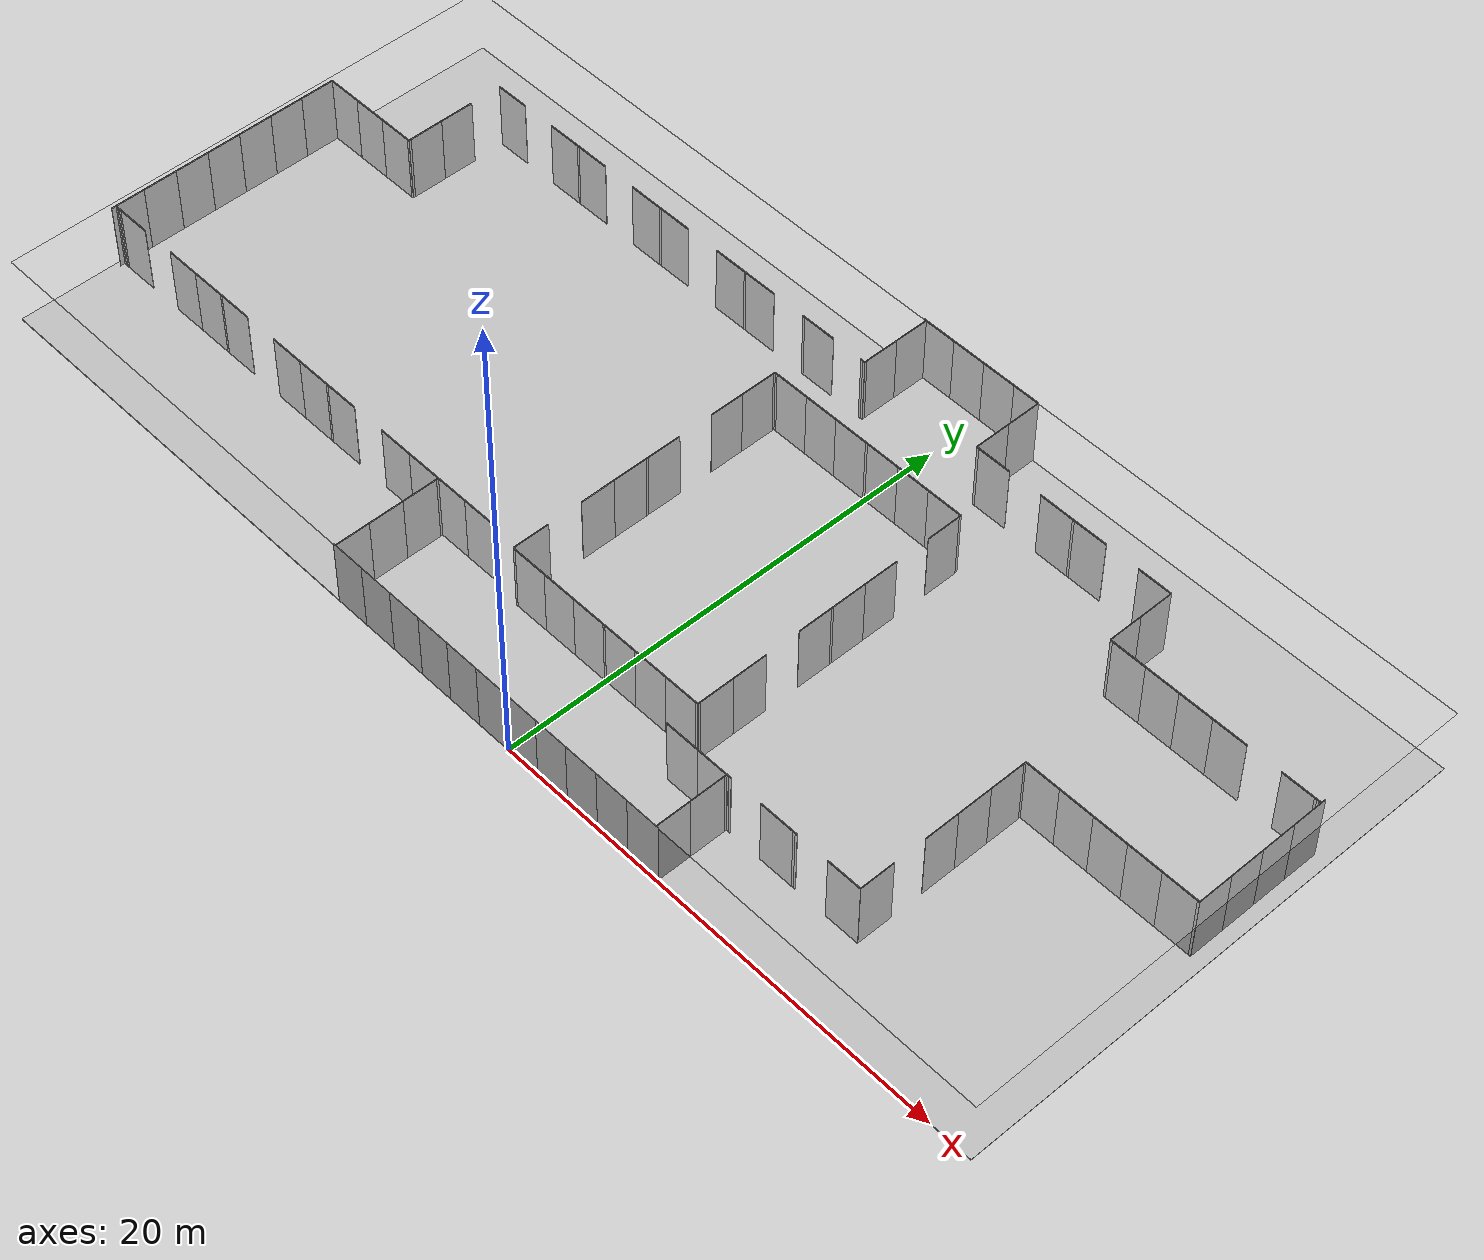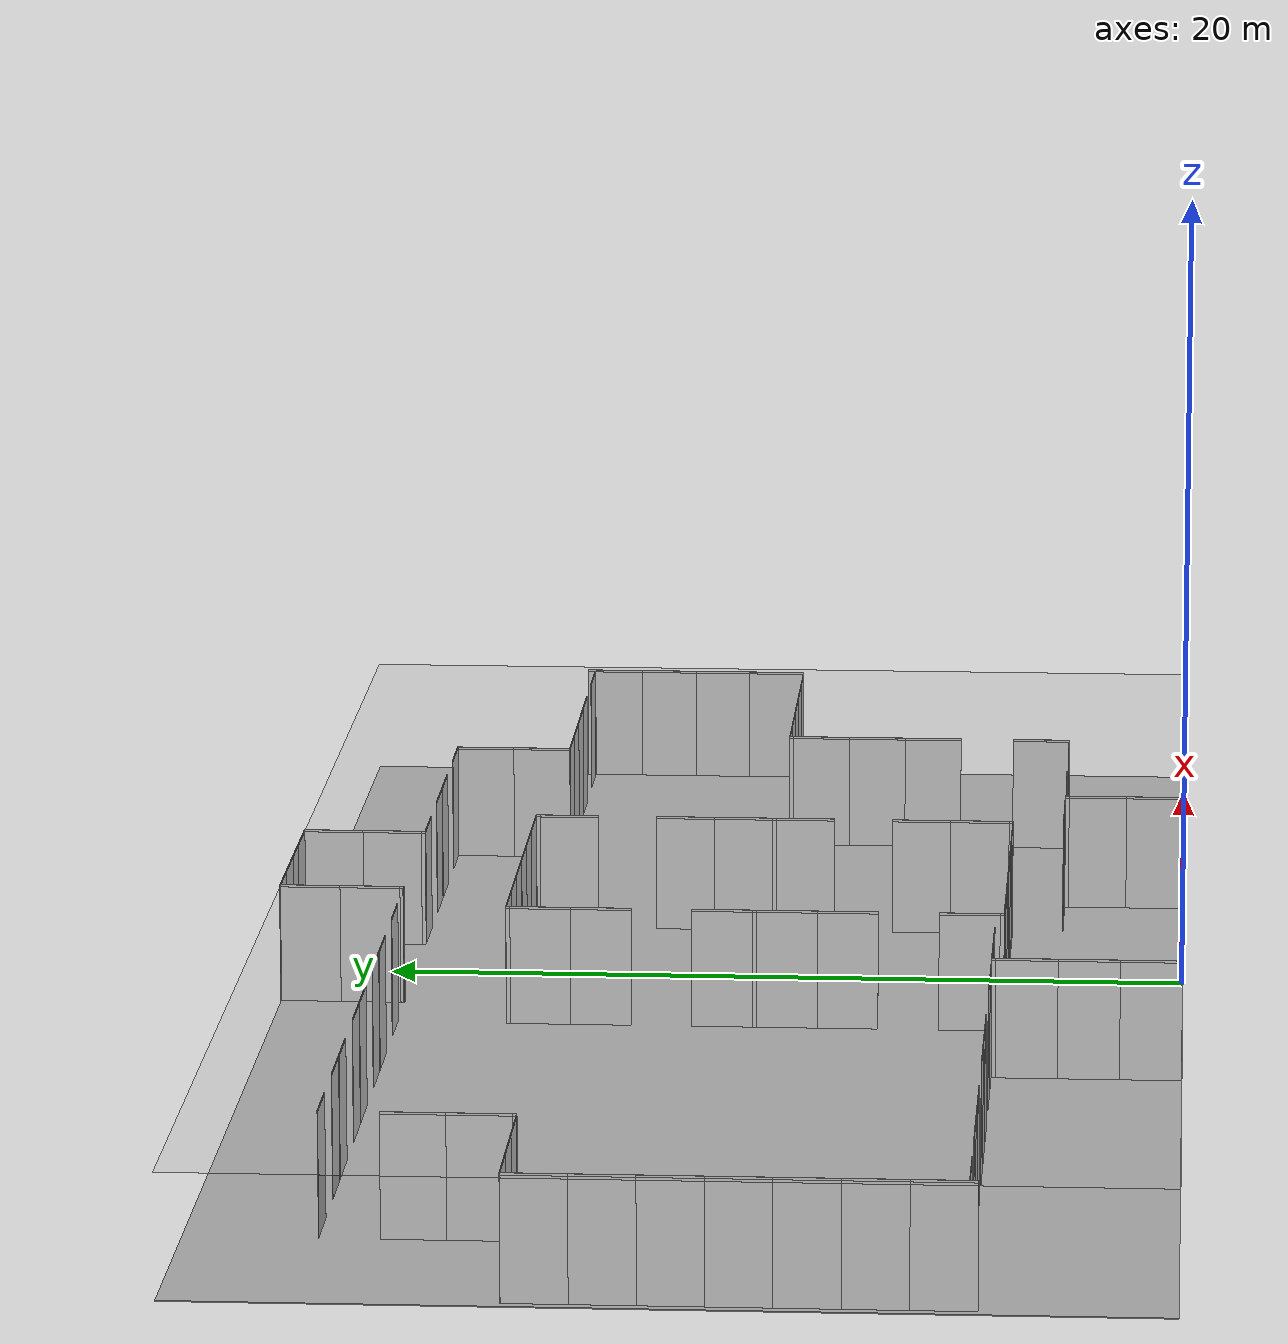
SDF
<sdf version="1.6">
 <world name="default">
  <physics type="ode">
   <real_time_update_rate>500.0</real_time_update_rate>
   <max_step_size>0.002</max_step_size>
   <real_time_factor>1</real_time_factor>
   <ode>
    <solver>
     <type>quick</type>
     <iters>300</iters>
     <precon_iters>0</precon_iters>
     <sor>1.400000</sor>
     <use_dynamic_moi_rescaling>1</use_dynamic_moi_rescaling>
    </solver>
    <constraints>
     <cfm>0.000000</cfm>
     <erp>0.800000</erp>
     <contact_max_correcting_vel>2000.000000</contact_max_correcting_vel>
     <contact_surface_layer>0.01000</contact_surface_layer>
    </constraints>
   </ode>
  </physics>
  <scene>
   <ambient>0.8 0.8 0.8 1.0</ambient>
   <background>0.66 0.77 0.84 1.0</background>
   <grid>0</grid>
   <origin_visual>0</origin_visual>
  </scene>
  <light name="directional_light" type="directional">
   <pose>0.0 0.0 -100.0 0 0 0</pose>
   <diffuse>0.5 0.5 0.5 1</diffuse>
   <specular>0.1 0.1 0.1 1</specular>
   <direction>0.1 0.1 -0.9</direction>
   <attenuation>
    <range>20</range>
    <constant>0.5</constant>
    <linear>0.01</linear>
    <quadratic>0.001</quadratic>
   </attenuation>
   <cast_shadows>0</cast_shadows>
  </light>
  <model name="ceiling">
   <pose>-2.9699999999999998
        11.25
        3.0
        0
        3.141592653589793
        0</pose>
   <static>true</static>
   <link name="link">
    <visual name="visual">
     <geometry><plane><normal>0 0 1</normal><size>49.5 22.5</size></plane></geometry>
     <material>
      <script>
       <uri>file://media/materials/scripts/</uri>
       <uri>file://media/materials/textures/</uri>
       <name>ServiceSim/Ceiling</name>
      </script>
     </material>
    </visual>
   </link>
  </model>
  <model name="floor">
   <pose>-2.9699999999999998
        11.25
        -0.001
        0
        0
        0</pose>
   <static>true</static>
   <link name="link">
    <visual name="visual">
     <geometry><plane><normal>0 0 1</normal><size>49.5 22.5</size></plane></geometry>
     <material>
      <script>
       <uri>file://media/materials/scripts/</uri>
       <uri>file://media/materials/textures/</uri>
       <name>ServiceSim/Hallway</name>
      </script>
     </material>
    </visual>
    <collision name="collision">
     <geometry><plane><normal>0 0 1</normal><size>49.5 22.5</size></plane></geometry>
     <surface><friction><ode><mu>1</mu><mu2>1</mu2></ode></friction></surface>
    </collision>
   </link>
  </model>
  <model name="walls">
   <static>true</static>
   <link name="link">
    <visual name="visual_1">
     <pose>-8.25
          0.0
          1.5
          0.0
          0.0
          0</pose>
     <geometry><box><size>1.5
              0.01
              3.0</size></box></geometry>
     <material>
      <script>
       <uri>file://media/materials/scripts/</uri>
       <uri>file://media/materials/textures/</uri>
       <name>ServiceSim/PlainWall</name>
      </script>
     </material>
    </visual>
    <collision name="collision_1">
     <pose>-8.25
          0.0
          1.5
          0.0
          0.0
          0</pose>
     <geometry><box><size>1.5
              0.01
              3.0</size></box></geometry>
    </collision>
    <visual name="visual_2">
     <pose>-6.75
          0.0
          1.5
          0.0
          0.0
          0</pose>
     <geometry><box><size>1.5
              0.01
              3.0</size></box></geometry>
     <material>
      <script>
       <uri>file://media/materials/scripts/</uri>
       <uri>file://media/materials/textures/</uri>
       <name>ServiceSim/PlainWall</name>
      </script>
     </material>
    </visual>
    <collision name="collision_2">
     <pose>-6.75
          0.0
          1.5
          0.0
          0.0
          0</pose>
     <geometry><box><size>1.5
              0.01
              3.0</size></box></geometry>
    </collision>
    <visual name="visual_3">
     <pose>-5.25
          0.0
          1.5
          0.0
          0.0
          0</pose>
     <geometry><box><size>1.5
              0.01
              3.0</size></box></geometry>
     <material>
      <script>
       <uri>file://media/materials/scripts/</uri>
       <uri>file://media/materials/textures/</uri>
       <name>ServiceSim/PlainWall</name>
      </script>
     </material>
    </visual>
    <collision name="collision_3">
     <pose>-5.25
          0.0
          1.5
          0.0
          0.0
          0</pose>
     <geometry><box><size>1.5
              0.01
              3.0</size></box></geometry>
    </collision>
    <visual name="visual_4">
     <pose>-3.75
          0.0
          1.5
          0.0
          0.0
          0</pose>
     <geometry><box><size>1.5
              0.01
              3.0</size></box></geometry>
     <material>
      <script>
       <uri>file://media/materials/scripts/</uri>
       <uri>file://media/materials/textures/</uri>
       <name>ServiceSim/PlainWall</name>
      </script>
     </material>
    </visual>
    <collision name="collision_4">
     <pose>-3.75
          0.0
          1.5
          0.0
          0.0
          0</pose>
     <geometry><box><size>1.5
              0.01
              3.0</size></box></geometry>
    </collision>
    <visual name="visual_5">
     <pose>-2.25
          0.0
          1.5
          0.0
          0.0
          0</pose>
     <geometry><box><size>1.5
              0.01
              3.0</size></box></geometry>
     <material>
      <script>
       <uri>file://media/materials/scripts/</uri>
       <uri>file://media/materials/textures/</uri>
       <name>ServiceSim/PlainWall</name>
      </script>
     </material>
    </visual>
    <collision name="collision_5">
     <pose>-2.25
          0.0
          1.5
          0.0
          0.0
          0</pose>
     <geometry><box><size>1.5
              0.01
              3.0</size></box></geometry>
    </collision>
    <visual name="visual_6">
     <pose>-0.75
          0.0
          1.5
          0.0
          0.0
          0</pose>
     <geometry><box><size>1.5
              0.01
              3.0</size></box></geometry>
     <material>
      <script>
       <uri>file://media/materials/scripts/</uri>
       <uri>file://media/materials/textures/</uri>
       <name>ServiceSim/Elevator</name>
      </script>
     </material>
    </visual>
    <collision name="collision_6">
     <pose>-0.75
          0.0
          1.5
          0.0
          0.0
          0</pose>
     <geometry><box><size>1.5
              0.01
              3.0</size></box></geometry>
    </collision>
    <visual name="visual_7">
     <pose>0.75
          0.0
          1.5
          0.0
          0.0
          0</pose>
     <geometry><box><size>1.5
              0.01
              3.0</size></box></geometry>
     <material>
      <script>
       <uri>file://media/materials/scripts/</uri>
       <uri>file://media/materials/textures/</uri>
       <name>ServiceSim/Elevator</name>
      </script>
     </material>
    </visual>
    <collision name="collision_7">
     <pose>0.75
          0.0
          1.5
          0.0
          0.0
          0</pose>
     <geometry><box><size>1.5
              0.01
              3.0</size></box></geometry>
    </collision>
    <visual name="visual_8">
     <pose>2.25
          0.0
          1.5
          0.0
          0.0
          0</pose>
     <geometry><box><size>1.5
              0.01
              3.0</size></box></geometry>
     <material>
      <script>
       <uri>file://media/materials/scripts/</uri>
       <uri>file://media/materials/textures/</uri>
       <name>ServiceSim/PlainWall</name>
      </script>
     </material>
    </visual>
    <collision name="collision_8">
     <pose>2.25
          0.0
          1.5
          0.0
          0.0
          0</pose>
     <geometry><box><size>1.5
              0.01
              3.0</size></box></geometry>
    </collision>
    <visual name="visual_9">
     <pose>3.75
          0.0
          1.5
          0.0
          0.0
          0</pose>
     <geometry><box><size>1.5
              0.01
              3.0</size></box></geometry>
     <material>
      <script>
       <uri>file://media/materials/scripts/</uri>
       <uri>file://media/materials/textures/</uri>
       <name>ServiceSim/PlainWall</name>
      </script>
     </material>
    </visual>
    <collision name="collision_9">
     <pose>3.75
          0.0
          1.5
          0.0
          0.0
          0</pose>
     <geometry><box><size>1.5
              0.01
              3.0</size></box></geometry>
    </collision>
    <visual name="visual_10">
     <pose>5.25
          0.0
          1.5
          0.0
          0.0
          0</pose>
     <geometry><box><size>1.5
              0.01
              3.0</size></box></geometry>
     <material>
      <script>
       <uri>file://media/materials/scripts/</uri>
       <uri>file://media/materials/textures/</uri>
       <name>ServiceSim/PlainWall</name>
      </script>
     </material>
    </visual>
    <collision name="collision_10">
     <pose>5.25
          0.0
          1.5
          0.0
          0.0
          0</pose>
     <geometry><box><size>1.5
              0.01
              3.0</size></box></geometry>
    </collision>
    <visual name="visual_11">
     <pose>6.749
          0.0
          1.5
          0.0
          0.0
          0</pose>
     <geometry><box><size>1.5
              0.01
              3.0</size></box></geometry>
     <material>
      <script>
       <uri>file://media/materials/scripts/</uri>
       <uri>file://media/materials/textures/</uri>
       <name>ServiceSim/PlainWall</name>
      </script>
     </material>
    </visual>
    <collision name="collision_11">
     <pose>6.749
          0.0
          1.5
          0.0
          0.0
          0</pose>
     <geometry><box><size>1.5
              0.01
              3.0</size></box></geometry>
    </collision>
    <visual name="visual_12">
     <pose>-8.25
          4.6
          1.5
          0.0
          0.0
          0</pose>
     <geometry><box><size>1.5
              0.01
              3.0</size></box></geometry>
     <material>
      <script>
       <uri>file://media/materials/scripts/</uri>
       <uri>file://media/materials/textures/</uri>
       <name>ServiceSim/PlainWall</name>
      </script>
     </material>
    </visual>
    <collision name="collision_12">
     <pose>-8.25
          4.6
          1.5
          0.0
          0.0
          0</pose>
     <geometry><box><size>1.5
              0.01
              3.0</size></box></geometry>
    </collision>
    <visual name="visual_13">
     <pose>-6.75
          4.6
          1.5
          0.0
          0.0
          0</pose>
     <geometry><box><size>1.5
              0.01
              3.0</size></box></geometry>
     <material>
      <script>
       <uri>file://media/materials/scripts/</uri>
       <uri>file://media/materials/textures/</uri>
       <name>ServiceSim/PlainWall</name>
      </script>
     </material>
    </visual>
    <collision name="collision_13">
     <pose>-6.75
          4.6
          1.5
          0.0
          0.0
          0</pose>
     <geometry><box><size>1.5
              0.01
              3.0</size></box></geometry>
    </collision>
    <visual name="visual_14">
     <pose>5.25
          3.1
          1.5
          0.0
          0.0
          0</pose>
     <geometry><box><size>1.5
              0.01
              3.0</size></box></geometry>
     <material>
      <script>
       <uri>file://media/materials/scripts/</uri>
       <uri>file://media/materials/textures/</uri>
       <name>ServiceSim/PlainWall</name>
      </script>
     </material>
    </visual>
    <collision name="collision_14">
     <pose>5.25
          3.1
          1.5
          0.0
          0.0
          0</pose>
     <geometry><box><size>1.5
              0.01
              3.0</size></box></geometry>
    </collision>
    <visual name="visual_15">
     <pose>6.75
          3.1
          1.5
          0.0
          0.0
          0</pose>
     <geometry><box><size>1.5
              0.01
              3.0</size></box></geometry>
     <material>
      <script>
       <uri>file://media/materials/scripts/</uri>
       <uri>file://media/materials/textures/</uri>
       <name>ServiceSim/PlainWall</name>
      </script>
     </material>
    </visual>
    <collision name="collision_15">
     <pose>6.75
          3.1
          1.5
          0.0
          0.0
          0</pose>
     <geometry><box><size>1.5
              0.01
              3.0</size></box></geometry>
    </collision>
    <visual name="visual_16">
     <pose>7.4
          0.75
          1.5
          0.0
          0.0
          1.5707963267948966</pose>
     <geometry><box><size>1.5
              0.01
              3.0</size></box></geometry>
     <material>
      <script>
       <uri>file://media/materials/scripts/</uri>
       <uri>file://media/materials/textures/</uri>
       <name>ServiceSim/PlainWall</name>
      </script>
     </material>
    </visual>
    <collision name="collision_16">
     <pose>7.4
          0.75
          1.5
          0.0
          0.0
          1.5707963267948966</pose>
     <geometry><box><size>1.5
              0.01
              3.0</size></box></geometry>
    </collision>
    <visual name="visual_17">
     <pose>7.4
          2.25
          1.5
          0.0
          0.0
          1.5707963267948966</pose>
     <geometry><box><size>1.5
              0.01
              3.0</size></box></geometry>
     <material>
      <script>
       <uri>file://media/materials/scripts/</uri>
       <uri>file://media/materials/textures/</uri>
       <name>ServiceSim/PlainWall</name>
      </script>
     </material>
    </visual>
    <collision name="collision_17">
     <pose>7.4
          2.25
          1.5
          0.0
          0.0
          1.5707963267948966</pose>
     <geometry><box><size>1.5
              0.01
              3.0</size></box></geometry>
    </collision>
    <visual name="visual_18">
     <pose>7.4
          3.05
          1.5
          0.0
          0.0
          1.5707963267948966</pose>
     <geometry><box><size>0.1
              0.01
              3.0</size></box></geometry>
     <material>
      <script>
       <uri>file://media/materials/scripts/</uri>
       <uri>file://media/materials/textures/</uri>
       <name>ServiceSim/PlainWall</name>
      </script>
     </material>
    </visual>
    <collision name="collision_18">
     <pose>7.4
          3.05
          1.5
          0.0
          0.0
          1.5707963267948966</pose>
     <geometry><box><size>0.1
              0.01
              3.0</size></box></geometry>
    </collision>
    <visual name="visual_19">
     <pose>7.45
          3.1
          1.5
          0.0
          0.0
          0</pose>
     <geometry><box><size>0.1
              0.01
              3.0</size></box></geometry>
     <material>
      <script>
       <uri>file://media/materials/scripts/</uri>
       <uri>file://media/materials/textures/</uri>
       <name>ServiceSim/PlainWall</name>
      </script>
     </material>
    </visual>
    <collision name="collision_19">
     <pose>7.45
          3.1
          1.5
          0.0
          0.0
          0</pose>
     <geometry><box><size>0.1
              0.01
              3.0</size></box></geometry>
    </collision>
    <visual name="visual_20">
     <pose>7.55
          3.1
          1.5
          0.0
          0.0
          0</pose>
     <geometry><box><size>0.1
              0.01
              3.0</size></box></geometry>
     <material>
      <script>
       <uri>file://media/materials/scripts/</uri>
       <uri>file://media/materials/textures/</uri>
       <name>ServiceSim/PlainWall</name>
      </script>
     </material>
    </visual>
    <collision name="collision_20">
     <pose>7.55
          3.1
          1.5
          0.0
          0.0
          0</pose>
     <geometry><box><size>0.1
              0.01
              3.0</size></box></geometry>
    </collision>
    <visual name="visual_21">
     <pose>9.75
          3.1
          1.5
          0.0
          0.0
          0</pose>
     <geometry><box><size>1.5
              0.01
              3.0</size></box></geometry>
     <material>
      <script>
       <uri>file://media/materials/scripts/</uri>
       <uri>file://media/materials/textures/</uri>
       <name>ServiceSim/PlainWall</name>
      </script>
     </material>
    </visual>
    <collision name="collision_21">
     <pose>9.75
          3.1
          1.5
          0.0
          0.0
          0</pose>
     <geometry><box><size>1.5
              0.01
              3.0</size></box></geometry>
    </collision>
    <visual name="visual_22">
     <pose>10.55
          3.1
          1.5
          0.0
          0.0
          0</pose>
     <geometry><box><size>0.1
              0.01
              3.0</size></box></geometry>
     <material>
      <script>
       <uri>file://media/materials/scripts/</uri>
       <uri>file://media/materials/textures/</uri>
       <name>ServiceSim/PlainWall</name>
      </script>
     </material>
    </visual>
    <collision name="collision_22">
     <pose>10.55
          3.1
          1.5
          0.0
          0.0
          0</pose>
     <geometry><box><size>0.1
              0.01
              3.0</size></box></geometry>
    </collision>
    <visual name="visual_23">
     <pose>10.65
          3.1
          1.5
          0.0
          0.0
          0</pose>
     <geometry><box><size>0.1
              0.01
              3.0</size></box></geometry>
     <material>
      <script>
       <uri>file://media/materials/scripts/</uri>
       <uri>file://media/materials/textures/</uri>
       <name>ServiceSim/PlainWall</name>
      </script>
     </material>
    </visual>
    <collision name="collision_23">
     <pose>10.65
          3.1
          1.5
          0.0
          0.0
          0</pose>
     <geometry><box><size>0.1
              0.01
              3.0</size></box></geometry>
    </collision>
    <visual name="visual_24">
     <pose>12.85
          3.1
          1.5
          0.0
          0.0
          0</pose>
     <geometry><box><size>1.5
              0.01
              3.0</size></box></geometry>
     <material>
      <script>
       <uri>file://media/materials/scripts/</uri>
       <uri>file://media/materials/textures/</uri>
       <name>ServiceSim/PlainWall</name>
      </script>
     </material>
    </visual>
    <collision name="collision_24">
     <pose>12.85
          3.1
          1.5
          0.0
          0.0
          0</pose>
     <geometry><box><size>1.5
              0.01
              3.0</size></box></geometry>
    </collision>
    <visual name="visual_25">
     <pose>13.6
          3.85
          1.5
          0.0
          0.0
          1.5707963267948966</pose>
     <geometry><box><size>1.5
              0.01
              3.0</size></box></geometry>
     <material>
      <script>
       <uri>file://media/materials/scripts/</uri>
       <uri>file://media/materials/textures/</uri>
       <name>ServiceSim/PlainWall</name>
      </script>
     </material>
    </visual>
    <collision name="collision_25">
     <pose>13.6
          3.85
          1.5
          0.0
          0.0
          1.5707963267948966</pose>
     <geometry><box><size>1.5
              0.01
              3.0</size></box></geometry>
    </collision>
    <visual name="visual_26">
     <pose>13.6
          6.75
          1.5
          0.0
          0.0
          1.5707963267948966</pose>
     <geometry><box><size>1.5
              0.01
              3.0</size></box></geometry>
     <material>
      <script>
       <uri>file://media/materials/scripts/</uri>
       <uri>file://media/materials/textures/</uri>
       <name>ServiceSim/PlainWall</name>
      </script>
     </material>
    </visual>
    <collision name="collision_26">
     <pose>13.6
          6.75
          1.5
          0.0
          0.0
          1.5707963267948966</pose>
     <geometry><box><size>1.5
              0.01
              3.0</size></box></geometry>
    </collision>
    <visual name="visual_27">
     <pose>13.6
          8.25
          1.5
          0.0
          0.0
          1.5707963267948966</pose>
     <geometry><box><size>1.5
              0.01
              3.0</size></box></geometry>
     <material>
      <script>
       <uri>file://media/materials/scripts/</uri>
       <uri>file://media/materials/textures/</uri>
       <name>ServiceSim/PlainWall</name>
      </script>
     </material>
    </visual>
    <collision name="collision_27">
     <pose>13.6
          8.25
          1.5
          0.0
          0.0
          1.5707963267948966</pose>
     <geometry><box><size>1.5
              0.01
              3.0</size></box></geometry>
    </collision>
    <visual name="visual_28">
     <pose>13.6
          9.75
          1.5
          0.0
          0.0
          1.5707963267948966</pose>
     <geometry><box><size>1.5
              0.01
              3.0</size></box></geometry>
     <material>
      <script>
       <uri>file://media/materials/scripts/</uri>
       <uri>file://media/materials/textures/</uri>
       <name>ServiceSim/PlainWall</name>
      </script>
     </material>
    </visual>
    <collision name="collision_28">
     <pose>13.6
          9.75
          1.5
          0.0
          0.0
          1.5707963267948966</pose>
     <geometry><box><size>1.5
              0.01
              3.0</size></box></geometry>
    </collision>
    <visual name="visual_29">
     <pose>13.6
          10.55
          1.5
          0.0
          0.0
          1.5707963267948966</pose>
     <geometry><box><size>0.1
              0.01
              3.0</size></box></geometry>
     <material>
      <script>
       <uri>file://media/materials/scripts/</uri>
       <uri>file://media/materials/textures/</uri>
       <name>ServiceSim/PlainWall</name>
      </script>
     </material>
    </visual>
    <collision name="collision_29">
     <pose>13.6
          10.55
          1.5
          0.0
          0.0
          1.5707963267948966</pose>
     <geometry><box><size>0.1
              0.01
              3.0</size></box></geometry>
    </collision>
    <visual name="visual_30">
     <pose>14.35
          10.6
          1.5
          0.0
          0.0
          0</pose>
     <geometry><box><size>1.5
              0.01
              3.0</size></box></geometry>
     <material>
      <script>
       <uri>file://media/materials/scripts/</uri>
       <uri>file://media/materials/textures/</uri>
       <name>ServiceSim/PlainWall</name>
      </script>
     </material>
    </visual>
    <collision name="collision_30">
     <pose>14.35
          10.6
          1.5
          0.0
          0.0
          0</pose>
     <geometry><box><size>1.5
              0.01
              3.0</size></box></geometry>
    </collision>
    <visual name="visual_31">
     <pose>15.85
          10.6
          1.5
          0.0
          0.0
          0</pose>
     <geometry><box><size>1.5
              0.01
              3.0</size></box></geometry>
     <material>
      <script>
       <uri>file://media/materials/scripts/</uri>
       <uri>file://media/materials/textures/</uri>
       <name>ServiceSim/PlainWall</name>
      </script>
     </material>
    </visual>
    <collision name="collision_31">
     <pose>15.85
          10.6
          1.5
          0.0
          0.0
          0</pose>
     <geometry><box><size>1.5
              0.01
              3.0</size></box></geometry>
    </collision>
    <visual name="visual_32">
     <pose>17.35
          10.6
          1.5
          0.0
          0.0
          0</pose>
     <geometry><box><size>1.5
              0.01
              3.0</size></box></geometry>
     <material>
      <script>
       <uri>file://media/materials/scripts/</uri>
       <uri>file://media/materials/textures/</uri>
       <name>ServiceSim/PlainWall</name>
      </script>
     </material>
    </visual>
    <collision name="collision_32">
     <pose>17.35
          10.6
          1.5
          0.0
          0.0
          0</pose>
     <geometry><box><size>1.5
              0.01
              3.0</size></box></geometry>
    </collision>
    <visual name="visual_33">
     <pose>18.85
          10.6
          1.5
          0.0
          0.0
          0</pose>
     <geometry><box><size>1.5
              0.01
              3.0</size></box></geometry>
     <material>
      <script>
       <uri>file://media/materials/scripts/</uri>
       <uri>file://media/materials/textures/</uri>
       <name>ServiceSim/PlainWall</name>
      </script>
     </material>
    </visual>
    <collision name="collision_33">
     <pose>18.85
          10.6
          1.5
          0.0
          0.0
          0</pose>
     <geometry><box><size>1.5
              0.01
              3.0</size></box></geometry>
    </collision>
    <visual name="visual_34">
     <pose>20.35
          10.6
          1.5
          0.0
          0.0
          0</pose>
     <geometry><box><size>1.5
              0.01
              3.0</size></box></geometry>
     <material>
      <script>
       <uri>file://media/materials/scripts/</uri>
       <uri>file://media/materials/textures/</uri>
       <name>ServiceSim/PlainWall</name>
      </script>
     </material>
    </visual>
    <collision name="collision_34">
     <pose>20.35
          10.6
          1.5
          0.0
          0.0
          0</pose>
     <geometry><box><size>1.5
              0.01
              3.0</size></box></geometry>
    </collision>
    <visual name="visual_35">
     <pose>21.150000000000002
          10.6
          1.5
          0.0
          0.0
          0</pose>
     <geometry><box><size>0.1
              0.01
              3.0</size></box></geometry>
     <material>
      <script>
       <uri>file://media/materials/scripts/</uri>
       <uri>file://media/materials/textures/</uri>
       <name>ServiceSim/PlainWall</name>
      </script>
     </material>
    </visual>
    <collision name="collision_35">
     <pose>21.150000000000002
          10.6
          1.5
          0.0
          0.0
          0</pose>
     <geometry><box><size>0.1
              0.01
              3.0</size></box></geometry>
    </collision>
    <visual name="visual_36">
     <pose>21.2
          11.35
          1.5
          0.0
          0.0
          1.5707963267948966</pose>
     <geometry><box><size>1.5
              0.01
              3.0</size></box></geometry>
     <material>
      <script>
       <uri>file://media/materials/scripts/</uri>
       <uri>file://media/materials/textures/</uri>
       <name>ServiceSim/PlainWall</name>
      </script>
     </material>
    </visual>
    <collision name="collision_36">
     <pose>21.2
          11.35
          1.5
          0.0
          0.0
          1.5707963267948966</pose>
     <geometry><box><size>1.5
              0.01
              3.0</size></box></geometry>
    </collision>
    <visual name="visual_37">
     <pose>21.2
          12.85
          1.5
          0.0
          0.0
          1.5707963267948966</pose>
     <geometry><box><size>1.5
              0.01
              3.0</size></box></geometry>
     <material>
      <script>
       <uri>file://media/materials/scripts/</uri>
       <uri>file://media/materials/textures/</uri>
       <name>ServiceSim/PlainWall</name>
      </script>
     </material>
    </visual>
    <collision name="collision_37">
     <pose>21.2
          12.85
          1.5
          0.0
          0.0
          1.5707963267948966</pose>
     <geometry><box><size>1.5
              0.01
              3.0</size></box></geometry>
    </collision>
    <visual name="visual_38">
     <pose>21.2
          14.35
          1.5
          0.0
          0.0
          1.5707963267948966</pose>
     <geometry><box><size>1.5
              0.01
              3.0</size></box></geometry>
     <material>
      <script>
       <uri>file://media/materials/scripts/</uri>
       <uri>file://media/materials/textures/</uri>
       <name>ServiceSim/PlainWall</name>
      </script>
     </material>
    </visual>
    <collision name="collision_38">
     <pose>21.2
          14.35
          1.5
          0.0
          0.0
          1.5707963267948966</pose>
     <geometry><box><size>1.5
              0.01
              3.0</size></box></geometry>
    </collision>
    <visual name="visual_39">
     <pose>21.2
          15.85
          1.5
          0.0
          0.0
          1.5707963267948966</pose>
     <geometry><box><size>1.5
              0.01
              3.0</size></box></geometry>
     <material>
      <script>
       <uri>file://media/materials/scripts/</uri>
       <uri>file://media/materials/textures/</uri>
       <name>ServiceSim/PlainWall</name>
      </script>
     </material>
    </visual>
    <collision name="collision_39">
     <pose>21.2
          15.85
          1.5
          0.0
          0.0
          1.5707963267948966</pose>
     <geometry><box><size>1.5
              0.01
              3.0</size></box></geometry>
    </collision>
    <visual name="visual_40">
     <pose>20.95
          16.4
          1.5
          0.0
          0.0
          0</pose>
     <geometry><box><size>0.1
              0.01
              3.0</size></box></geometry>
     <material>
      <script>
       <uri>file://media/materials/scripts/</uri>
       <uri>file://media/materials/textures/</uri>
       <name>ServiceSim/PlainWall</name>
      </script>
     </material>
    </visual>
    <collision name="collision_40">
     <pose>20.95
          16.4
          1.5
          0.0
          0.0
          0</pose>
     <geometry><box><size>0.1
              0.01
              3.0</size></box></geometry>
    </collision>
    <visual name="visual_41">
     <pose>21.05
          16.4
          1.5
          0.0
          0.0
          0</pose>
     <geometry><box><size>0.1
              0.01
              3.0</size></box></geometry>
     <material>
      <script>
       <uri>file://media/materials/scripts/</uri>
       <uri>file://media/materials/textures/</uri>
       <name>ServiceSim/PlainWall</name>
      </script>
     </material>
    </visual>
    <collision name="collision_41">
     <pose>21.05
          16.4
          1.5
          0.0
          0.0
          0</pose>
     <geometry><box><size>0.1
              0.01
              3.0</size></box></geometry>
    </collision>
    <visual name="visual_42">
     <pose>21.150000000000002
          16.4
          1.5
          0.0
          0.0
          0</pose>
     <geometry><box><size>0.1
              0.01
              3.0</size></box></geometry>
     <material>
      <script>
       <uri>file://media/materials/scripts/</uri>
       <uri>file://media/materials/textures/</uri>
       <name>ServiceSim/PlainWall</name>
      </script>
     </material>
    </visual>
    <collision name="collision_42">
     <pose>21.150000000000002
          16.4
          1.5
          0.0
          0.0
          0</pose>
     <geometry><box><size>0.1
              0.01
              3.0</size></box></geometry>
    </collision>
    <visual name="visual_43">
     <pose>20.25
          16.4
          1.5
          0.0
          0.0
          0</pose>
     <geometry><box><size>1.5
              0.01
              3.0</size></box></geometry>
     <material>
      <script>
       <uri>file://media/materials/scripts/</uri>
       <uri>file://media/materials/textures/</uri>
       <name>ServiceSim/PlainWall</name>
      </script>
     </material>
    </visual>
    <collision name="collision_43">
     <pose>20.25
          16.4
          1.5
          0.0
          0.0
          0</pose>
     <geometry><box><size>1.5
              0.01
              3.0</size></box></geometry>
    </collision>
    <visual name="visual_44">
     <pose>17.25
          16.4
          1.5
          0.0
          0.0
          0</pose>
     <geometry><box><size>1.5
              0.01
              3.0</size></box></geometry>
     <material>
      <script>
       <uri>file://media/materials/scripts/</uri>
       <uri>file://media/materials/textures/</uri>
       <name>ServiceSim/PlainWall</name>
      </script>
     </material>
    </visual>
    <collision name="collision_44">
     <pose>17.25
          16.4
          1.5
          0.0
          0.0
          0</pose>
     <geometry><box><size>1.5
              0.01
              3.0</size></box></geometry>
    </collision>
    <visual name="visual_45">
     <pose>15.75
          16.4
          1.5
          0.0
          0.0
          0</pose>
     <geometry><box><size>1.5
              0.01
              3.0</size></box></geometry>
     <material>
      <script>
       <uri>file://media/materials/scripts/</uri>
       <uri>file://media/materials/textures/</uri>
       <name>ServiceSim/PlainWall</name>
      </script>
     </material>
    </visual>
    <collision name="collision_45">
     <pose>15.75
          16.4
          1.5
          0.0
          0.0
          0</pose>
     <geometry><box><size>1.5
              0.01
              3.0</size></box></geometry>
    </collision>
    <visual name="visual_46">
     <pose>14.25
          16.4
          1.5
          0.0
          0.0
          0</pose>
     <geometry><box><size>1.5
              0.01
              3.0</size></box></geometry>
     <material>
      <script>
       <uri>file://media/materials/scripts/</uri>
       <uri>file://media/materials/textures/</uri>
       <name>ServiceSim/PlainWall</name>
      </script>
     </material>
    </visual>
    <collision name="collision_46">
     <pose>14.25
          16.4
          1.5
          0.0
          0.0
          0</pose>
     <geometry><box><size>1.5
              0.01
              3.0</size></box></geometry>
    </collision>
    <visual name="visual_47">
     <pose>12.75
          16.4
          1.5
          0.0
          0.0
          0</pose>
     <geometry><box><size>1.5
              0.01
              3.0</size></box></geometry>
     <material>
      <script>
       <uri>file://media/materials/scripts/</uri>
       <uri>file://media/materials/textures/</uri>
       <name>ServiceSim/PlainWall</name>
      </script>
     </material>
    </visual>
    <collision name="collision_47">
     <pose>12.75
          16.4
          1.5
          0.0
          0.0
          0</pose>
     <geometry><box><size>1.5
              0.01
              3.0</size></box></geometry>
    </collision>
    <visual name="visual_48">
     <pose>11.950000000000001
          16.4
          1.5
          0.0
          0.0
          0</pose>
     <geometry><box><size>0.1
              0.01
              3.0</size></box></geometry>
     <material>
      <script>
       <uri>file://media/materials/scripts/</uri>
       <uri>file://media/materials/textures/</uri>
       <name>ServiceSim/PlainWall</name>
      </script>
     </material>
    </visual>
    <collision name="collision_48">
     <pose>11.950000000000001
          16.4
          1.5
          0.0
          0.0
          0</pose>
     <geometry><box><size>0.1
              0.01
              3.0</size></box></geometry>
    </collision>
    <visual name="visual_49">
     <pose>11.9
          17.15
          1.5
          0.0
          0.0
          1.5707963267948966</pose>
     <geometry><box><size>1.5
              0.01
              3.0</size></box></geometry>
     <material>
      <script>
       <uri>file://media/materials/scripts/</uri>
       <uri>file://media/materials/textures/</uri>
       <name>ServiceSim/PlainWall</name>
      </script>
     </material>
    </visual>
    <collision name="collision_49">
     <pose>11.9
          17.15
          1.5
          0.0
          0.0
          1.5707963267948966</pose>
     <geometry><box><size>1.5
              0.01
              3.0</size></box></geometry>
    </collision>
    <visual name="visual_50">
     <pose>11.9
          18.65
          1.5
          0.0
          0.0
          1.5707963267948966</pose>
     <geometry><box><size>1.5
              0.01
              3.0</size></box></geometry>
     <material>
      <script>
       <uri>file://media/materials/scripts/</uri>
       <uri>file://media/materials/textures/</uri>
       <name>ServiceSim/PlainWall</name>
      </script>
     </material>
    </visual>
    <collision name="collision_50">
     <pose>11.9
          18.65
          1.5
          0.0
          0.0
          1.5707963267948966</pose>
     <geometry><box><size>1.5
              0.01
              3.0</size></box></geometry>
    </collision>
    <visual name="visual_51">
     <pose>11.15
          19.4
          1.5
          0.0
          0.0
          0</pose>
     <geometry><box><size>1.5
              0.01
              3.0</size></box></geometry>
     <material>
      <script>
       <uri>file://media/materials/scripts/</uri>
       <uri>file://media/materials/textures/</uri>
       <name>ServiceSim/PlainWall</name>
      </script>
     </material>
    </visual>
    <collision name="collision_51">
     <pose>11.15
          19.4
          1.5
          0.0
          0.0
          0</pose>
     <geometry><box><size>1.5
              0.01
              3.0</size></box></geometry>
    </collision>
    <visual name="visual_52">
     <pose>8.15
          19.4
          1.5
          0.0
          0.0
          0</pose>
     <geometry><box><size>1.5
              0.01
              3.0</size></box></geometry>
     <material>
      <script>
       <uri>file://media/materials/scripts/</uri>
       <uri>file://media/materials/textures/</uri>
       <name>ServiceSim/PlainWall</name>
      </script>
     </material>
    </visual>
    <collision name="collision_52">
     <pose>8.15
          19.4
          1.5
          0.0
          0.0
          0</pose>
     <geometry><box><size>1.5
              0.01
              3.0</size></box></geometry>
    </collision>
    <visual name="visual_53">
     <pose>7.35
          19.4
          1.5
          0.0
          0.0
          0</pose>
     <geometry><box><size>0.1
              0.01
              3.0</size></box></geometry>
     <material>
      <script>
       <uri>file://media/materials/scripts/</uri>
       <uri>file://media/materials/textures/</uri>
       <name>ServiceSim/PlainWall</name>
      </script>
     </material>
    </visual>
    <collision name="collision_53">
     <pose>7.35
          19.4
          1.5
          0.0
          0.0
          0</pose>
     <geometry><box><size>0.1
              0.01
              3.0</size></box></geometry>
    </collision>
    <visual name="visual_54">
     <pose>6.55
          19.4
          1.5
          0.0
          0.0
          0</pose>
     <geometry><box><size>1.5
              0.01
              3.0</size></box></geometry>
     <material>
      <script>
       <uri>file://media/materials/scripts/</uri>
       <uri>file://media/materials/textures/</uri>
       <name>ServiceSim/PlainWall</name>
      </script>
     </material>
    </visual>
    <collision name="collision_54">
     <pose>6.55
          19.4
          1.5
          0.0
          0.0
          0</pose>
     <geometry><box><size>1.5
              0.01
              3.0</size></box></geometry>
    </collision>
    <visual name="visual_55">
     <pose>3.55
          19.4
          1.5
          0.0
          0.0
          0</pose>
     <geometry><box><size>1.5
              0.01
              3.0</size></box></geometry>
     <material>
      <script>
       <uri>file://media/materials/scripts/</uri>
       <uri>file://media/materials/textures/</uri>
       <name>ServiceSim/PlainWall</name>
      </script>
     </material>
    </visual>
    <collision name="collision_55">
     <pose>3.55
          19.4
          1.5
          0.0
          0.0
          0</pose>
     <geometry><box><size>1.5
              0.01
              3.0</size></box></geometry>
    </collision>
    <visual name="visual_56">
     <pose>2.75
          19.4
          1.5
          0.0
          0.0
          0</pose>
     <geometry><box><size>0.1
              0.01
              3.0</size></box></geometry>
     <material>
      <script>
       <uri>file://media/materials/scripts/</uri>
       <uri>file://media/materials/textures/</uri>
       <name>ServiceSim/PlainWall</name>
      </script>
     </material>
    </visual>
    <collision name="collision_56">
     <pose>2.75
          19.4
          1.5
          0.0
          0.0
          0</pose>
     <geometry><box><size>0.1
              0.01
              3.0</size></box></geometry>
    </collision>
    <visual name="visual_57">
     <pose>2.7
          19.45
          1.5
          0.0
          0.0
          1.5707963267948966</pose>
     <geometry><box><size>0.1
              0.01
              3.0</size></box></geometry>
     <material>
      <script>
       <uri>file://media/materials/scripts/</uri>
       <uri>file://media/materials/textures/</uri>
       <name>ServiceSim/PlainWall</name>
      </script>
     </material>
    </visual>
    <collision name="collision_57">
     <pose>2.7
          19.45
          1.5
          0.0
          0.0
          1.5707963267948966</pose>
     <geometry><box><size>0.1
              0.01
              3.0</size></box></geometry>
    </collision>
    <visual name="visual_58">
     <pose>2.7
          20.25
          1.5
          0.0
          0.0
          1.5707963267948966</pose>
     <geometry><box><size>1.5
              0.01
              3.0</size></box></geometry>
     <material>
      <script>
       <uri>file://media/materials/scripts/</uri>
       <uri>file://media/materials/textures/</uri>
       <name>ServiceSim/PlainWall</name>
      </script>
     </material>
    </visual>
    <collision name="collision_58">
     <pose>2.7
          20.25
          1.5
          0.0
          0.0
          1.5707963267948966</pose>
     <geometry><box><size>1.5
              0.01
              3.0</size></box></geometry>
    </collision>
    <visual name="visual_59">
     <pose>2.7
          21.75
          1.5
          0.0
          0.0
          1.5707963267948966</pose>
     <geometry><box><size>1.5
              0.01
              3.0</size></box></geometry>
     <material>
      <script>
       <uri>file://media/materials/scripts/</uri>
       <uri>file://media/materials/textures/</uri>
       <name>ServiceSim/PlainWall</name>
      </script>
     </material>
    </visual>
    <collision name="collision_59">
     <pose>2.7
          21.75
          1.5
          0.0
          0.0
          1.5707963267948966</pose>
     <geometry><box><size>1.5
              0.01
              3.0</size></box></geometry>
    </collision>
    <visual name="visual_60">
     <pose>1.95
          22.5
          1.5
          0.0
          0.0
          0</pose>
     <geometry><box><size>1.5
              0.01
              3.0</size></box></geometry>
     <material>
      <script>
       <uri>file://media/materials/scripts/</uri>
       <uri>file://media/materials/textures/</uri>
       <name>ServiceSim/PlainWall</name>
      </script>
     </material>
    </visual>
    <collision name="collision_60">
     <pose>1.95
          22.5
          1.5
          0.0
          0.0
          0</pose>
     <geometry><box><size>1.5
              0.01
              3.0</size></box></geometry>
    </collision>
    <visual name="visual_61">
     <pose>0.75
          22.5
          1.5
          0.0
          0.0
          0</pose>
     <geometry><box><size>1.5
              0.01
              3.0</size></box></geometry>
     <material>
      <script>
       <uri>file://media/materials/scripts/</uri>
       <uri>file://media/materials/textures/</uri>
       <name>ServiceSim/PlainWall</name>
      </script>
     </material>
    </visual>
    <collision name="collision_61">
     <pose>0.75
          22.5
          1.5
          0.0
          0.0
          0</pose>
     <geometry><box><size>1.5
              0.01
              3.0</size></box></geometry>
    </collision>
    <visual name="visual_62">
     <pose>-0.75
          22.5
          1.5
          0.0
          0.0
          0</pose>
     <geometry><box><size>1.5
              0.01
              3.0</size></box></geometry>
     <material>
      <script>
       <uri>file://media/materials/scripts/</uri>
       <uri>file://media/materials/textures/</uri>
       <name>ServiceSim/PlainWall</name>
      </script>
     </material>
    </visual>
    <collision name="collision_62">
     <pose>-0.75
          22.5
          1.5
          0.0
          0.0
          0</pose>
     <geometry><box><size>1.5
              0.01
              3.0</size></box></geometry>
    </collision>
    <visual name="visual_63">
     <pose>-2.25
          22.5
          1.5
          0.0
          0.0
          0</pose>
     <geometry><box><size>1.5
              0.01
              3.0</size></box></geometry>
     <material>
      <script>
       <uri>file://media/materials/scripts/</uri>
       <uri>file://media/materials/textures/</uri>
       <name>ServiceSim/Door</name>
      </script>
     </material>
    </visual>
    <collision name="collision_63">
     <pose>-2.25
          22.5
          1.5
          0.0
          0.0
          0</pose>
     <geometry><box><size>1.5
              0.01
              3.0</size></box></geometry>
    </collision>
    <visual name="visual_64">
     <pose>-2.9
          21.75
          1.5
          0.0
          0.0
          1.5707963267948966</pose>
     <geometry><box><size>1.5
              0.01
              3.0</size></box></geometry>
     <material>
      <script>
       <uri>file://media/materials/scripts/</uri>
       <uri>file://media/materials/textures/</uri>
       <name>ServiceSim/PlainWall</name>
      </script>
     </material>
    </visual>
    <collision name="collision_64">
     <pose>-2.9
          21.75
          1.5
          0.0
          0.0
          1.5707963267948966</pose>
     <geometry><box><size>1.5
              0.01
              3.0</size></box></geometry>
    </collision>
    <visual name="visual_65">
     <pose>-2.9
          20.25
          1.5
          0.0
          0.0
          1.5707963267948966</pose>
     <geometry><box><size>1.5
              0.01
              3.0</size></box></geometry>
     <material>
      <script>
       <uri>file://media/materials/scripts/</uri>
       <uri>file://media/materials/textures/</uri>
       <name>ServiceSim/PlainWall</name>
      </script>
     </material>
    </visual>
    <collision name="collision_65">
     <pose>-2.9
          20.25
          1.5
          0.0
          0.0
          1.5707963267948966</pose>
     <geometry><box><size>1.5
              0.01
              3.0</size></box></geometry>
    </collision>
    <visual name="visual_66">
     <pose>-2.9
          19.45
          1.5
          0.0
          0.0
          1.5707963267948966</pose>
     <geometry><box><size>0.1
              0.01
              3.0</size></box></geometry>
     <material>
      <script>
       <uri>file://media/materials/scripts/</uri>
       <uri>file://media/materials/textures/</uri>
       <name>ServiceSim/PlainWall</name>
      </script>
     </material>
    </visual>
    <collision name="collision_66">
     <pose>-2.9
          19.45
          1.5
          0.0
          0.0
          1.5707963267948966</pose>
     <geometry><box><size>0.1
              0.01
              3.0</size></box></geometry>
    </collision>
    <visual name="visual_67">
     <pose>-2.95
          19.4
          1.5
          0.0
          0.0
          0</pose>
     <geometry><box><size>0.1
              0.01
              3.0</size></box></geometry>
     <material>
      <script>
       <uri>file://media/materials/scripts/</uri>
       <uri>file://media/materials/textures/</uri>
       <name>ServiceSim/PlainWall</name>
      </script>
     </material>
    </visual>
    <collision name="collision_67">
     <pose>-2.95
          19.4
          1.5
          0.0
          0.0
          0</pose>
     <geometry><box><size>0.1
              0.01
              3.0</size></box></geometry>
    </collision>
    <visual name="visual_68">
     <pose>-3.0500000000000003
          19.4
          1.5
          0.0
          0.0
          0</pose>
     <geometry><box><size>0.1
              0.01
              3.0</size></box></geometry>
     <material>
      <script>
       <uri>file://media/materials/scripts/</uri>
       <uri>file://media/materials/textures/</uri>
       <name>ServiceSim/PlainWall</name>
      </script>
     </material>
    </visual>
    <collision name="collision_68">
     <pose>-3.0500000000000003
          19.4
          1.5
          0.0
          0.0
          0</pose>
     <geometry><box><size>0.1
              0.01
              3.0</size></box></geometry>
    </collision>
    <visual name="visual_69">
     <pose>-5.25
          19.4
          1.5
          0.0
          0.0
          0</pose>
     <geometry><box><size>1.5
              0.01
              3.0</size></box></geometry>
     <material>
      <script>
       <uri>file://media/materials/scripts/</uri>
       <uri>file://media/materials/textures/</uri>
       <name>ServiceSim/PlainWall</name>
      </script>
     </material>
    </visual>
    <collision name="collision_69">
     <pose>-5.25
          19.4
          1.5
          0.0
          0.0
          0</pose>
     <geometry><box><size>1.5
              0.01
              3.0</size></box></geometry>
    </collision>
    <visual name="visual_70">
     <pose>-6.05
          19.4
          1.5
          0.0
          0.0
          0</pose>
     <geometry><box><size>0.1
              0.01
              3.0</size></box></geometry>
     <material>
      <script>
       <uri>file://media/materials/scripts/</uri>
       <uri>file://media/materials/textures/</uri>
       <name>ServiceSim/PlainWall</name>
      </script>
     </material>
    </visual>
    <collision name="collision_70">
     <pose>-6.05
          19.4
          1.5
          0.0
          0.0
          0</pose>
     <geometry><box><size>0.1
              0.01
              3.0</size></box></geometry>
    </collision>
    <visual name="visual_71">
     <pose>-8.35
          19.4
          1.5
          0.0
          0.0
          0</pose>
     <geometry><box><size>1.5
              0.01
              3.0</size></box></geometry>
     <material>
      <script>
       <uri>file://media/materials/scripts/</uri>
       <uri>file://media/materials/textures/</uri>
       <name>ServiceSim/PlainWall</name>
      </script>
     </material>
    </visual>
    <collision name="collision_71">
     <pose>-8.35
          19.4
          1.5
          0.0
          0.0
          0</pose>
     <geometry><box><size>1.5
              0.01
              3.0</size></box></geometry>
    </collision>
    <visual name="visual_72">
     <pose>-9.149999999999999
          19.4
          1.5
          0.0
          0.0
          0</pose>
     <geometry><box><size>0.1
              0.01
              3.0</size></box></geometry>
     <material>
      <script>
       <uri>file://media/materials/scripts/</uri>
       <uri>file://media/materials/textures/</uri>
       <name>ServiceSim/PlainWall</name>
      </script>
     </material>
    </visual>
    <collision name="collision_72">
     <pose>-9.149999999999999
          19.4
          1.5
          0.0
          0.0
          0</pose>
     <geometry><box><size>0.1
              0.01
              3.0</size></box></geometry>
    </collision>
    <visual name="visual_73">
     <pose>-9.95
          19.4
          1.5
          0.0
          0.0
          0</pose>
     <geometry><box><size>1.5
              0.01
              3.0</size></box></geometry>
     <material>
      <script>
       <uri>file://media/materials/scripts/</uri>
       <uri>file://media/materials/textures/</uri>
       <name>ServiceSim/PlainWall</name>
      </script>
     </material>
    </visual>
    <collision name="collision_73">
     <pose>-9.95
          19.4
          1.5
          0.0
          0.0
          0</pose>
     <geometry><box><size>1.5
              0.01
              3.0</size></box></geometry>
    </collision>
    <visual name="visual_74">
     <pose>-12.95
          19.4
          1.5
          0.0
          0.0
          0</pose>
     <geometry><box><size>1.5
              0.01
              3.0</size></box></geometry>
     <material>
      <script>
       <uri>file://media/materials/scripts/</uri>
       <uri>file://media/materials/textures/</uri>
       <name>ServiceSim/PlainWall</name>
      </script>
     </material>
    </visual>
    <collision name="collision_74">
     <pose>-12.95
          19.4
          1.5
          0.0
          0.0
          0</pose>
     <geometry><box><size>1.5
              0.01
              3.0</size></box></geometry>
    </collision>
    <visual name="visual_75">
     <pose>-13.75
          19.4
          1.5
          0.0
          0.0
          0</pose>
     <geometry><box><size>0.1
              0.01
              3.0</size></box></geometry>
     <material>
      <script>
       <uri>file://media/materials/scripts/</uri>
       <uri>file://media/materials/textures/</uri>
       <name>ServiceSim/PlainWall</name>
      </script>
     </material>
    </visual>
    <collision name="collision_75">
     <pose>-13.75
          19.4
          1.5
          0.0
          0.0
          0</pose>
     <geometry><box><size>0.1
              0.01
              3.0</size></box></geometry>
    </collision>
    <visual name="visual_76">
     <pose>-14.55
          19.4
          1.5
          0.0
          0.0
          0</pose>
     <geometry><box><size>1.5
              0.01
              3.0</size></box></geometry>
     <material>
      <script>
       <uri>file://media/materials/scripts/</uri>
       <uri>file://media/materials/textures/</uri>
       <name>ServiceSim/PlainWall</name>
      </script>
     </material>
    </visual>
    <collision name="collision_76">
     <pose>-14.55
          19.4
          1.5
          0.0
          0.0
          0</pose>
     <geometry><box><size>1.5
              0.01
              3.0</size></box></geometry>
    </collision>
    <visual name="visual_77">
     <pose>-18.349999999999998
          19.4
          1.5
          0.0
          0.0
          0</pose>
     <geometry><box><size>0.1
              0.01
              3.0</size></box></geometry>
     <material>
      <script>
       <uri>file://media/materials/scripts/</uri>
       <uri>file://media/materials/textures/</uri>
       <name>ServiceSim/PlainWall</name>
      </script>
     </material>
    </visual>
    <collision name="collision_77">
     <pose>-18.349999999999998
          19.4
          1.5
          0.0
          0.0
          0</pose>
     <geometry><box><size>0.1
              0.01
              3.0</size></box></geometry>
    </collision>
    <visual name="visual_78">
     <pose>-17.55
          19.4
          1.5
          0.0
          0.0
          0</pose>
     <geometry><box><size>1.5
              0.01
              3.0</size></box></geometry>
     <material>
      <script>
       <uri>file://media/materials/scripts/</uri>
       <uri>file://media/materials/textures/</uri>
       <name>ServiceSim/PlainWall</name>
      </script>
     </material>
    </visual>
    <collision name="collision_78">
     <pose>-17.55
          19.4
          1.5
          0.0
          0.0
          0</pose>
     <geometry><box><size>1.5
              0.01
              3.0</size></box></geometry>
    </collision>
    <visual name="visual_79">
     <pose>-19.15
          19.4
          1.5
          0.0
          0.0
          0</pose>
     <geometry><box><size>1.5
              0.01
              3.0</size></box></geometry>
     <material>
      <script>
       <uri>file://media/materials/scripts/</uri>
       <uri>file://media/materials/textures/</uri>
       <name>ServiceSim/PlainWall</name>
      </script>
     </material>
    </visual>
    <collision name="collision_79">
     <pose>-19.15
          19.4
          1.5
          0.0
          0.0
          0</pose>
     <geometry><box><size>1.5
              0.01
              3.0</size></box></geometry>
    </collision>
    <visual name="visual_80">
     <pose>-22.15
          19.4
          1.5
          0.0
          0.0
          0</pose>
     <geometry><box><size>1.5
              0.01
              3.0</size></box></geometry>
     <material>
      <script>
       <uri>file://media/materials/scripts/</uri>
       <uri>file://media/materials/textures/</uri>
       <name>ServiceSim/PlainWall</name>
      </script>
     </material>
    </visual>
    <collision name="collision_80">
     <pose>-22.15
          19.4
          1.5
          0.0
          0.0
          0</pose>
     <geometry><box><size>1.5
              0.01
              3.0</size></box></geometry>
    </collision>
    <visual name="visual_81">
     <pose>-22.9
          17.25
          1.5
          0.0
          0.0
          1.5707963267948966</pose>
     <geometry><box><size>1.5
              0.01
              3.0</size></box></geometry>
     <material>
      <script>
       <uri>file://media/materials/scripts/</uri>
       <uri>file://media/materials/textures/</uri>
       <name>ServiceSim/PlainWall</name>
      </script>
     </material>
    </visual>
    <collision name="collision_81">
     <pose>-22.9
          17.25
          1.5
          0.0
          0.0
          1.5707963267948966</pose>
     <geometry><box><size>1.5
              0.01
              3.0</size></box></geometry>
    </collision>
    <visual name="visual_82">
     <pose>-22.9
          15.75
          1.5
          0.0
          0.0
          1.5707963267948966</pose>
     <geometry><box><size>1.5
              0.01
              3.0</size></box></geometry>
     <material>
      <script>
       <uri>file://media/materials/scripts/</uri>
       <uri>file://media/materials/textures/</uri>
       <name>ServiceSim/PlainWall</name>
      </script>
     </material>
    </visual>
    <collision name="collision_82">
     <pose>-22.9
          15.75
          1.5
          0.0
          0.0
          1.5707963267948966</pose>
     <geometry><box><size>1.5
              0.01
              3.0</size></box></geometry>
    </collision>
    <visual name="visual_83">
     <pose>-22.9
          14.950000000000001
          1.5
          0.0
          0.0
          1.5707963267948966</pose>
     <geometry><box><size>0.1
              0.01
              3.0</size></box></geometry>
     <material>
      <script>
       <uri>file://media/materials/scripts/</uri>
       <uri>file://media/materials/textures/</uri>
       <name>ServiceSim/PlainWall</name>
      </script>
     </material>
    </visual>
    <collision name="collision_83">
     <pose>-22.9
          14.950000000000001
          1.5
          0.0
          0.0
          1.5707963267948966</pose>
     <geometry><box><size>0.1
              0.01
              3.0</size></box></geometry>
    </collision>
    <visual name="visual_84">
     <pose>-22.95
          14.9
          1.5
          0.0
          0.0
          0</pose>
     <geometry><box><size>0.1
              0.01
              3.0</size></box></geometry>
     <material>
      <script>
       <uri>file://media/materials/scripts/</uri>
       <uri>file://media/materials/textures/</uri>
       <name>ServiceSim/PlainWall</name>
      </script>
     </material>
    </visual>
    <collision name="collision_84">
     <pose>-22.95
          14.9
          1.5
          0.0
          0.0
          0</pose>
     <geometry><box><size>0.1
              0.01
              3.0</size></box></geometry>
    </collision>
    <visual name="visual_85">
     <pose>-23.75
          14.9
          1.5
          0.0
          0.0
          0</pose>
     <geometry><box><size>1.5
              0.01
              3.0</size></box></geometry>
     <material>
      <script>
       <uri>file://media/materials/scripts/</uri>
       <uri>file://media/materials/textures/</uri>
       <name>ServiceSim/PlainWall</name>
      </script>
     </material>
    </visual>
    <collision name="collision_85">
     <pose>-23.75
          14.9
          1.5
          0.0
          0.0
          0</pose>
     <geometry><box><size>1.5
              0.01
              3.0</size></box></geometry>
    </collision>
    <visual name="visual_86">
     <pose>-25.25
          14.9
          1.5
          0.0
          0.0
          0</pose>
     <geometry><box><size>1.5
              0.01
              3.0</size></box></geometry>
     <material>
      <script>
       <uri>file://media/materials/scripts/</uri>
       <uri>file://media/materials/textures/</uri>
       <name>ServiceSim/PlainWall</name>
      </script>
     </material>
    </visual>
    <collision name="collision_86">
     <pose>-25.25
          14.9
          1.5
          0.0
          0.0
          0</pose>
     <geometry><box><size>1.5
              0.01
              3.0</size></box></geometry>
    </collision>
    <visual name="visual_87">
     <pose>-26.75
          14.9
          1.5
          0.0
          0.0
          0</pose>
     <geometry><box><size>1.5
              0.01
              3.0</size></box></geometry>
     <material>
      <script>
       <uri>file://media/materials/scripts/</uri>
       <uri>file://media/materials/textures/</uri>
       <name>ServiceSim/PlainWall</name>
      </script>
     </material>
    </visual>
    <collision name="collision_87">
     <pose>-26.75
          14.9
          1.5
          0.0
          0.0
          0</pose>
     <geometry><box><size>1.5
              0.01
              3.0</size></box></geometry>
    </collision>
    <visual name="visual_88">
     <pose>-27.5
          14.15
          1.5
          0.0
          0.0
          1.5707963267948966</pose>
     <geometry><box><size>1.5
              0.01
              3.0</size></box></geometry>
     <material>
      <script>
       <uri>file://media/materials/scripts/</uri>
       <uri>file://media/materials/textures/</uri>
       <name>ServiceSim/PlainWall</name>
      </script>
     </material>
    </visual>
    <collision name="collision_88">
     <pose>-27.5
          14.15
          1.5
          0.0
          0.0
          1.5707963267948966</pose>
     <geometry><box><size>1.5
              0.01
              3.0</size></box></geometry>
    </collision>
    <visual name="visual_89">
     <pose>-27.5
          12.65
          1.5
          0.0
          0.0
          1.5707963267948966</pose>
     <geometry><box><size>1.5
              0.01
              3.0</size></box></geometry>
     <material>
      <script>
       <uri>file://media/materials/scripts/</uri>
       <uri>file://media/materials/textures/</uri>
       <name>ServiceSim/PlainWall</name>
      </script>
     </material>
    </visual>
    <collision name="collision_89">
     <pose>-27.5
          12.65
          1.5
          0.0
          0.0
          1.5707963267948966</pose>
     <geometry><box><size>1.5
              0.01
              3.0</size></box></geometry>
    </collision>
    <visual name="visual_90">
     <pose>-27.5
          11.15
          1.5
          0.0
          0.0
          1.5707963267948966</pose>
     <geometry><box><size>1.5
              0.01
              3.0</size></box></geometry>
     <material>
      <script>
       <uri>file://media/materials/scripts/</uri>
       <uri>file://media/materials/textures/</uri>
       <name>ServiceSim/PlainWall</name>
      </script>
     </material>
    </visual>
    <collision name="collision_90">
     <pose>-27.5
          11.15
          1.5
          0.0
          0.0
          1.5707963267948966</pose>
     <geometry><box><size>1.5
              0.01
              3.0</size></box></geometry>
    </collision>
    <visual name="visual_91">
     <pose>-27.5
          9.65
          1.5
          0.0
          0.0
          1.5707963267948966</pose>
     <geometry><box><size>1.5
              0.01
              3.0</size></box></geometry>
     <material>
      <script>
       <uri>file://media/materials/scripts/</uri>
       <uri>file://media/materials/textures/</uri>
       <name>ServiceSim/PlainWall</name>
      </script>
     </material>
    </visual>
    <collision name="collision_91">
     <pose>-27.5
          9.65
          1.5
          0.0
          0.0
          1.5707963267948966</pose>
     <geometry><box><size>1.5
              0.01
              3.0</size></box></geometry>
    </collision>
    <visual name="visual_92">
     <pose>-27.5
          8.15
          1.5
          0.0
          0.0
          1.5707963267948966</pose>
     <geometry><box><size>1.5
              0.01
              3.0</size></box></geometry>
     <material>
      <script>
       <uri>file://media/materials/scripts/</uri>
       <uri>file://media/materials/textures/</uri>
       <name>ServiceSim/PlainWall</name>
      </script>
     </material>
    </visual>
    <collision name="collision_92">
     <pose>-27.5
          8.15
          1.5
          0.0
          0.0
          1.5707963267948966</pose>
     <geometry><box><size>1.5
              0.01
              3.0</size></box></geometry>
    </collision>
    <visual name="visual_93">
     <pose>-27.5
          6.65
          1.5
          0.0
          0.0
          1.5707963267948966</pose>
     <geometry><box><size>1.5
              0.01
              3.0</size></box></geometry>
     <material>
      <script>
       <uri>file://media/materials/scripts/</uri>
       <uri>file://media/materials/textures/</uri>
       <name>ServiceSim/PlainWall</name>
      </script>
     </material>
    </visual>
    <collision name="collision_93">
     <pose>-27.5
          6.65
          1.5
          0.0
          0.0
          1.5707963267948966</pose>
     <geometry><box><size>1.5
              0.01
              3.0</size></box></geometry>
    </collision>
    <visual name="visual_94">
     <pose>-27.5
          5.15
          1.5
          0.0
          0.0
          1.5707963267948966</pose>
     <geometry><box><size>1.5
              0.01
              3.0</size></box></geometry>
     <material>
      <script>
       <uri>file://media/materials/scripts/</uri>
       <uri>file://media/materials/textures/</uri>
       <name>ServiceSim/PlainWall</name>
      </script>
     </material>
    </visual>
    <collision name="collision_94">
     <pose>-27.5
          5.15
          1.5
          0.0
          0.0
          1.5707963267948966</pose>
     <geometry><box><size>1.5
              0.01
              3.0</size></box></geometry>
    </collision>
    <visual name="visual_95">
     <pose>-27.45
          4.6
          1.5
          0.0
          0.0
          0</pose>
     <geometry><box><size>0.1
              0.01
              3.0</size></box></geometry>
     <material>
      <script>
       <uri>file://media/materials/scripts/</uri>
       <uri>file://media/materials/textures/</uri>
       <name>ServiceSim/PlainWall</name>
      </script>
     </material>
    </visual>
    <collision name="collision_95">
     <pose>-27.45
          4.6
          1.5
          0.0
          0.0
          0</pose>
     <geometry><box><size>0.1
              0.01
              3.0</size></box></geometry>
    </collision>
    <visual name="visual_96">
     <pose>-27.349999999999998
          4.6
          1.5
          0.0
          0.0
          0</pose>
     <geometry><box><size>0.1
              0.01
              3.0</size></box></geometry>
     <material>
      <script>
       <uri>file://media/materials/scripts/</uri>
       <uri>file://media/materials/textures/</uri>
       <name>ServiceSim/PlainWall</name>
      </script>
     </material>
    </visual>
    <collision name="collision_96">
     <pose>-27.349999999999998
          4.6
          1.5
          0.0
          0.0
          0</pose>
     <geometry><box><size>0.1
              0.01
              3.0</size></box></geometry>
    </collision>
    <visual name="visual_97">
     <pose>-27.25
          4.6
          1.5
          0.0
          0.0
          0</pose>
     <geometry><box><size>0.1
              0.01
              3.0</size></box></geometry>
     <material>
      <script>
       <uri>file://media/materials/scripts/</uri>
       <uri>file://media/materials/textures/</uri>
       <name>ServiceSim/PlainWall</name>
      </script>
     </material>
    </visual>
    <collision name="collision_97">
     <pose>-27.25
          4.6
          1.5
          0.0
          0.0
          0</pose>
     <geometry><box><size>0.1
              0.01
              3.0</size></box></geometry>
    </collision>
    <visual name="visual_98">
     <pose>-26.45
          4.6
          1.5
          0.0
          0.0
          0</pose>
     <geometry><box><size>1.5
              0.01
              3.0</size></box></geometry>
     <material>
      <script>
       <uri>file://media/materials/scripts/</uri>
       <uri>file://media/materials/textures/</uri>
       <name>ServiceSim/PlainWall</name>
      </script>
     </material>
    </visual>
    <collision name="collision_98">
     <pose>-26.45
          4.6
          1.5
          0.0
          0.0
          0</pose>
     <geometry><box><size>1.5
              0.01
              3.0</size></box></geometry>
    </collision>
    <visual name="visual_99">
     <pose>-23.45
          4.6
          1.5
          0.0
          0.0
          0</pose>
     <geometry><box><size>1.5
              0.01
              3.0</size></box></geometry>
     <material>
      <script>
       <uri>file://media/materials/scripts/</uri>
       <uri>file://media/materials/textures/</uri>
       <name>ServiceSim/PlainWall</name>
      </script>
     </material>
    </visual>
    <collision name="collision_99">
     <pose>-23.45
          4.6
          1.5
          0.0
          0.0
          0</pose>
     <geometry><box><size>1.5
              0.01
              3.0</size></box></geometry>
    </collision>
    <visual name="visual_100">
     <pose>-21.95
          4.6
          1.5
          0.0
          0.0
          0</pose>
     <geometry><box><size>1.5
              0.01
              3.0</size></box></geometry>
     <material>
      <script>
       <uri>file://media/materials/scripts/</uri>
       <uri>file://media/materials/textures/</uri>
       <name>ServiceSim/PlainWall</name>
      </script>
     </material>
    </visual>
    <collision name="collision_100">
     <pose>-21.95
          4.6
          1.5
          0.0
          0.0
          0</pose>
     <geometry><box><size>1.5
              0.01
              3.0</size></box></geometry>
    </collision>
    <visual name="visual_101">
     <pose>-21.15
          4.6
          1.5
          0.0
          0.0
          0</pose>
     <geometry><box><size>0.1
              0.01
              3.0</size></box></geometry>
     <material>
      <script>
       <uri>file://media/materials/scripts/</uri>
       <uri>file://media/materials/textures/</uri>
       <name>ServiceSim/PlainWall</name>
      </script>
     </material>
    </visual>
    <collision name="collision_101">
     <pose>-21.15
          4.6
          1.5
          0.0
          0.0
          0</pose>
     <geometry><box><size>0.1
              0.01
              3.0</size></box></geometry>
    </collision>
    <visual name="visual_102">
     <pose>-20.35
          4.6
          1.5
          0.0
          0.0
          0</pose>
     <geometry><box><size>1.5
              0.01
              3.0</size></box></geometry>
     <material>
      <script>
       <uri>file://media/materials/scripts/</uri>
       <uri>file://media/materials/textures/</uri>
       <name>ServiceSim/PlainWall</name>
      </script>
     </material>
    </visual>
    <collision name="collision_102">
     <pose>-20.35
          4.6
          1.5
          0.0
          0.0
          0</pose>
     <geometry><box><size>1.5
              0.01
              3.0</size></box></geometry>
    </collision>
    <visual name="visual_103">
     <pose>-17.35
          4.6
          1.5
          0.0
          0.0
          0</pose>
     <geometry><box><size>1.5
              0.01
              3.0</size></box></geometry>
     <material>
      <script>
       <uri>file://media/materials/scripts/</uri>
       <uri>file://media/materials/textures/</uri>
       <name>ServiceSim/PlainWall</name>
      </script>
     </material>
    </visual>
    <collision name="collision_103">
     <pose>-17.35
          4.6
          1.5
          0.0
          0.0
          0</pose>
     <geometry><box><size>1.5
              0.01
              3.0</size></box></geometry>
    </collision>
    <visual name="visual_104">
     <pose>-15.850000000000001
          4.6
          1.5
          0.0
          0.0
          0</pose>
     <geometry><box><size>1.5
              0.01
              3.0</size></box></geometry>
     <material>
      <script>
       <uri>file://media/materials/scripts/</uri>
       <uri>file://media/materials/textures/</uri>
       <name>ServiceSim/PlainWall</name>
      </script>
     </material>
    </visual>
    <collision name="collision_104">
     <pose>-15.850000000000001
          4.6
          1.5
          0.0
          0.0
          0</pose>
     <geometry><box><size>1.5
              0.01
              3.0</size></box></geometry>
    </collision>
    <visual name="visual_105">
     <pose>-15.049999999999999
          4.6
          1.5
          0.0
          0.0
          0</pose>
     <geometry><box><size>0.1
              0.01
              3.0</size></box></geometry>
     <material>
      <script>
       <uri>file://media/materials/scripts/</uri>
       <uri>file://media/materials/textures/</uri>
       <name>ServiceSim/PlainWall</name>
      </script>
     </material>
    </visual>
    <collision name="collision_105">
     <pose>-15.049999999999999
          4.6
          1.5
          0.0
          0.0
          0</pose>
     <geometry><box><size>0.1
              0.01
              3.0</size></box></geometry>
    </collision>
    <visual name="visual_106">
     <pose>-14.25
          4.6
          1.5
          0.0
          0.0
          0</pose>
     <geometry><box><size>1.5
              0.01
              3.0</size></box></geometry>
     <material>
      <script>
       <uri>file://media/materials/scripts/</uri>
       <uri>file://media/materials/textures/</uri>
       <name>ServiceSim/PlainWall</name>
      </script>
     </material>
    </visual>
    <collision name="collision_106">
     <pose>-14.25
          4.6
          1.5
          0.0
          0.0
          0</pose>
     <geometry><box><size>1.5
              0.01
              3.0</size></box></geometry>
    </collision>
    <visual name="visual_107">
     <pose>-11.25
          4.6
          1.5
          0.0
          0.0
          0</pose>
     <geometry><box><size>1.5
              0.01
              3.0</size></box></geometry>
     <material>
      <script>
       <uri>file://media/materials/scripts/</uri>
       <uri>file://media/materials/textures/</uri>
       <name>ServiceSim/PlainWall</name>
      </script>
     </material>
    </visual>
    <collision name="collision_107">
     <pose>-11.25
          4.6
          1.5
          0.0
          0.0
          0</pose>
     <geometry><box><size>1.5
              0.01
              3.0</size></box></geometry>
    </collision>
    <visual name="visual_108">
     <pose>-9.75
          4.6
          1.5
          0.0
          0.0
          0</pose>
     <geometry><box><size>1.5
              0.01
              3.0</size></box></geometry>
     <material>
      <script>
       <uri>file://media/materials/scripts/</uri>
       <uri>file://media/materials/textures/</uri>
       <name>ServiceSim/PlainWall</name>
      </script>
     </material>
    </visual>
    <collision name="collision_108">
     <pose>-9.75
          4.6
          1.5
          0.0
          0.0
          0</pose>
     <geometry><box><size>1.5
              0.01
              3.0</size></box></geometry>
    </collision>
    <visual name="visual_109">
     <pose>-8.95
          4.6
          1.5
          0.0
          0.0
          0</pose>
     <geometry><box><size>0.1
              0.01
              3.0</size></box></geometry>
     <material>
      <script>
       <uri>file://media/materials/scripts/</uri>
       <uri>file://media/materials/textures/</uri>
       <name>ServiceSim/PlainWall</name>
      </script>
     </material>
    </visual>
    <collision name="collision_109">
     <pose>-8.95
          4.6
          1.5
          0.0
          0.0
          0</pose>
     <geometry><box><size>0.1
              0.01
              3.0</size></box></geometry>
    </collision>
    <visual name="visual_110">
     <pose>-8.9
          4.55
          1.5
          0.0
          0.0
          1.5707963267948966</pose>
     <geometry><box><size>0.1
              0.01
              3.0</size></box></geometry>
     <material>
      <script>
       <uri>file://media/materials/scripts/</uri>
       <uri>file://media/materials/textures/</uri>
       <name>ServiceSim/PlainWall</name>
      </script>
     </material>
    </visual>
    <collision name="collision_110">
     <pose>-8.9
          4.55
          1.5
          0.0
          0.0
          1.5707963267948966</pose>
     <geometry><box><size>0.1
              0.01
              3.0</size></box></geometry>
    </collision>
    <visual name="visual_111">
     <pose>-8.9
          3.75
          1.5
          0.0
          0.0
          1.5707963267948966</pose>
     <geometry><box><size>1.5
              0.01
              3.0</size></box></geometry>
     <material>
      <script>
       <uri>file://media/materials/scripts/</uri>
       <uri>file://media/materials/textures/</uri>
       <name>ServiceSim/PlainWall</name>
      </script>
     </material>
    </visual>
    <collision name="collision_111">
     <pose>-8.9
          3.75
          1.5
          0.0
          0.0
          1.5707963267948966</pose>
     <geometry><box><size>1.5
              0.01
              3.0</size></box></geometry>
    </collision>
    <visual name="visual_112">
     <pose>-8.9
          2.25
          1.5
          0.0
          0.0
          1.5707963267948966</pose>
     <geometry><box><size>1.5
              0.01
              3.0</size></box></geometry>
     <material>
      <script>
       <uri>file://media/materials/scripts/</uri>
       <uri>file://media/materials/textures/</uri>
       <name>ServiceSim/PlainWall</name>
      </script>
     </material>
    </visual>
    <collision name="collision_112">
     <pose>-8.9
          2.25
          1.5
          0.0
          0.0
          1.5707963267948966</pose>
     <geometry><box><size>1.5
              0.01
              3.0</size></box></geometry>
    </collision>
    <visual name="visual_113">
     <pose>-8.9
          0.75
          1.5
          0.0
          0.0
          1.5707963267948966</pose>
     <geometry><box><size>1.5
              0.01
              3.0</size></box></geometry>
     <material>
      <script>
       <uri>file://media/materials/scripts/</uri>
       <uri>file://media/materials/textures/</uri>
       <name>ServiceSim/PlainWall</name>
      </script>
     </material>
    </visual>
    <collision name="collision_113">
     <pose>-8.9
          0.75
          1.5
          0.0
          0.0
          1.5707963267948966</pose>
     <geometry><box><size>1.5
              0.01
              3.0</size></box></geometry>
    </collision>
    <visual name="visual_114">
     <pose>-4.65
          4.4
          1.5
          0.0
          0.0
          0</pose>
     <geometry><box><size>0.1
              0.01
              3.0</size></box></geometry>
     <material>
      <script>
       <uri>file://media/materials/scripts/</uri>
       <uri>file://media/materials/textures/</uri>
       <name>ServiceSim/PlainWall</name>
      </script>
     </material>
    </visual>
    <collision name="collision_114">
     <pose>-4.65
          4.4
          1.5
          0.0
          0.0
          0</pose>
     <geometry><box><size>0.1
              0.01
              3.0</size></box></geometry>
    </collision>
    <visual name="visual_115">
     <pose>-3.8499999999999996
          4.4
          1.5
          0.0
          0.0
          0</pose>
     <geometry><box><size>1.5
              0.01
              3.0</size></box></geometry>
     <material>
      <script>
       <uri>file://media/materials/scripts/</uri>
       <uri>file://media/materials/textures/</uri>
       <name>ServiceSim/PlainWall</name>
      </script>
     </material>
    </visual>
    <collision name="collision_115">
     <pose>-3.8499999999999996
          4.4
          1.5
          0.0
          0.0
          0</pose>
     <geometry><box><size>1.5
              0.01
              3.0</size></box></geometry>
    </collision>
    <visual name="visual_116">
     <pose>-2.35
          4.4
          1.5
          0.0
          0.0
          0</pose>
     <geometry><box><size>1.5
              0.01
              3.0</size></box></geometry>
     <material>
      <script>
       <uri>file://media/materials/scripts/</uri>
       <uri>file://media/materials/textures/</uri>
       <name>ServiceSim/PlainWall</name>
      </script>
     </material>
    </visual>
    <collision name="collision_116">
     <pose>-2.35
          4.4
          1.5
          0.0
          0.0
          0</pose>
     <geometry><box><size>1.5
              0.01
              3.0</size></box></geometry>
    </collision>
    <visual name="visual_117">
     <pose>-0.8500000000000001
          4.4
          1.5
          0.0
          0.0
          0</pose>
     <geometry><box><size>1.5
              0.01
              3.0</size></box></geometry>
     <material>
      <script>
       <uri>file://media/materials/scripts/</uri>
       <uri>file://media/materials/textures/</uri>
       <name>ServiceSim/PlainWall</name>
      </script>
     </material>
    </visual>
    <collision name="collision_117">
     <pose>-0.8500000000000001
          4.4
          1.5
          0.0
          0.0
          0</pose>
     <geometry><box><size>1.5
              0.01
              3.0</size></box></geometry>
    </collision>
    <visual name="visual_118">
     <pose>-0.05
          4.4
          1.5
          0.0
          0.0
          0</pose>
     <geometry><box><size>0.1
              0.01
              3.0</size></box></geometry>
     <material>
      <script>
       <uri>file://media/materials/scripts/</uri>
       <uri>file://media/materials/textures/</uri>
       <name>ServiceSim/PlainWall</name>
      </script>
     </material>
    </visual>
    <collision name="collision_118">
     <pose>-0.05
          4.4
          1.5
          0.0
          0.0
          0</pose>
     <geometry><box><size>0.1
              0.01
              3.0</size></box></geometry>
    </collision>
    <visual name="visual_119">
     <pose>0.75
          4.4
          1.5
          0.0
          0.0
          0</pose>
     <geometry><box><size>1.5
              0.01
              3.0</size></box></geometry>
     <material>
      <script>
       <uri>file://media/materials/scripts/</uri>
       <uri>file://media/materials/textures/</uri>
       <name>ServiceSim/PlainWall</name>
      </script>
     </material>
    </visual>
    <collision name="collision_119">
     <pose>0.75
          4.4
          1.5
          0.0
          0.0
          0</pose>
     <geometry><box><size>1.5
              0.01
              3.0</size></box></geometry>
    </collision>
    <visual name="visual_120">
     <pose>2.25
          4.4
          1.5
          0.0
          0.0
          0</pose>
     <geometry><box><size>1.5
              0.01
              3.0</size></box></geometry>
     <material>
      <script>
       <uri>file://media/materials/scripts/</uri>
       <uri>file://media/materials/textures/</uri>
       <name>ServiceSim/PlainWall</name>
      </script>
     </material>
    </visual>
    <collision name="collision_120">
     <pose>2.25
          4.4
          1.5
          0.0
          0.0
          0</pose>
     <geometry><box><size>1.5
              0.01
              3.0</size></box></geometry>
    </collision>
    <visual name="visual_121">
     <pose>3.75
          4.4
          1.5
          0.0
          0.0
          0</pose>
     <geometry><box><size>1.5
              0.01
              3.0</size></box></geometry>
     <material>
      <script>
       <uri>file://media/materials/scripts/</uri>
       <uri>file://media/materials/textures/</uri>
       <name>ServiceSim/PlainWall</name>
      </script>
     </material>
    </visual>
    <collision name="collision_121">
     <pose>3.75
          4.4
          1.5
          0.0
          0.0
          0</pose>
     <geometry><box><size>1.5
              0.01
              3.0</size></box></geometry>
    </collision>
    <visual name="visual_122">
     <pose>4.55
          4.4
          1.5
          0.0
          0.0
          0</pose>
     <geometry><box><size>0.1
              0.01
              3.0</size></box></geometry>
     <material>
      <script>
       <uri>file://media/materials/scripts/</uri>
       <uri>file://media/materials/textures/</uri>
       <name>ServiceSim/PlainWall</name>
      </script>
     </material>
    </visual>
    <collision name="collision_122">
     <pose>4.55
          4.4
          1.5
          0.0
          0.0
          0</pose>
     <geometry><box><size>0.1
              0.01
              3.0</size></box></geometry>
    </collision>
    <visual name="visual_123">
     <pose>4.6
          4.45
          1.5
          0.0
          0.0
          1.5707963267948966</pose>
     <geometry><box><size>0.1
              0.01
              3.0</size></box></geometry>
     <material>
      <script>
       <uri>file://media/materials/scripts/</uri>
       <uri>file://media/materials/textures/</uri>
       <name>ServiceSim/PlainWall</name>
      </script>
     </material>
    </visual>
    <collision name="collision_123">
     <pose>4.6
          4.45
          1.5
          0.0
          0.0
          1.5707963267948966</pose>
     <geometry><box><size>0.1
              0.01
              3.0</size></box></geometry>
    </collision>
    <visual name="visual_124">
     <pose>4.6
          5.25
          1.5
          0.0
          0.0
          1.5707963267948966</pose>
     <geometry><box><size>1.5
              0.01
              3.0</size></box></geometry>
     <material>
      <script>
       <uri>file://media/materials/scripts/</uri>
       <uri>file://media/materials/textures/</uri>
       <name>ServiceSim/PlainWall</name>
      </script>
     </material>
    </visual>
    <collision name="collision_124">
     <pose>4.6
          5.25
          1.5
          0.0
          0.0
          1.5707963267948966</pose>
     <geometry><box><size>1.5
              0.01
              3.0</size></box></geometry>
    </collision>
    <visual name="visual_125">
     <pose>4.6
          6.75
          1.5
          0.0
          0.0
          1.5707963267948966</pose>
     <geometry><box><size>1.5
              0.01
              3.0</size></box></geometry>
     <material>
      <script>
       <uri>file://media/materials/scripts/</uri>
       <uri>file://media/materials/textures/</uri>
       <name>ServiceSim/PlainWall</name>
      </script>
     </material>
    </visual>
    <collision name="collision_125">
     <pose>4.6
          6.75
          1.5
          0.0
          0.0
          1.5707963267948966</pose>
     <geometry><box><size>1.5
              0.01
              3.0</size></box></geometry>
    </collision>
    <visual name="visual_126">
     <pose>4.6
          9.75
          1.5
          0.0
          0.0
          1.5707963267948966</pose>
     <geometry><box><size>1.5
              0.01
              3.0</size></box></geometry>
     <material>
      <script>
       <uri>file://media/materials/scripts/</uri>
       <uri>file://media/materials/textures/</uri>
       <name>ServiceSim/PlainWall</name>
      </script>
     </material>
    </visual>
    <collision name="collision_126">
     <pose>4.6
          9.75
          1.5
          0.0
          0.0
          1.5707963267948966</pose>
     <geometry><box><size>1.5
              0.01
              3.0</size></box></geometry>
    </collision>
    <visual name="visual_127">
     <pose>4.6
          10.55
          1.5
          0.0
          0.0
          1.5707963267948966</pose>
     <geometry><box><size>0.1
              0.01
              3.0</size></box></geometry>
     <material>
      <script>
       <uri>file://media/materials/scripts/</uri>
       <uri>file://media/materials/textures/</uri>
       <name>ServiceSim/PlainWall</name>
      </script>
     </material>
    </visual>
    <collision name="collision_127">
     <pose>4.6
          10.55
          1.5
          0.0
          0.0
          1.5707963267948966</pose>
     <geometry><box><size>0.1
              0.01
              3.0</size></box></geometry>
    </collision>
    <visual name="visual_128">
     <pose>4.6
          11.35
          1.5
          0.0
          0.0
          1.5707963267948966</pose>
     <geometry><box><size>1.5
              0.01
              3.0</size></box></geometry>
     <material>
      <script>
       <uri>file://media/materials/scripts/</uri>
       <uri>file://media/materials/textures/</uri>
       <name>ServiceSim/PlainWall</name>
      </script>
     </material>
    </visual>
    <collision name="collision_128">
     <pose>4.6
          11.35
          1.5
          0.0
          0.0
          1.5707963267948966</pose>
     <geometry><box><size>1.5
              0.01
              3.0</size></box></geometry>
    </collision>
    <visual name="visual_129">
     <pose>4.6
          12.85
          1.5
          0.0
          0.0
          1.5707963267948966</pose>
     <geometry><box><size>1.5
              0.01
              3.0</size></box></geometry>
     <material>
      <script>
       <uri>file://media/materials/scripts/</uri>
       <uri>file://media/materials/textures/</uri>
       <name>ServiceSim/PlainWall</name>
      </script>
     </material>
    </visual>
    <collision name="collision_129">
     <pose>4.6
          12.85
          1.5
          0.0
          0.0
          1.5707963267948966</pose>
     <geometry><box><size>1.5
              0.01
              3.0</size></box></geometry>
    </collision>
    <visual name="visual_130">
     <pose>4.6
          15.85
          1.5
          0.0
          0.0
          1.5707963267948966</pose>
     <geometry><box><size>1.5
              0.01
              3.0</size></box></geometry>
     <material>
      <script>
       <uri>file://media/materials/scripts/</uri>
       <uri>file://media/materials/textures/</uri>
       <name>ServiceSim/PlainWall</name>
      </script>
     </material>
    </visual>
    <collision name="collision_130">
     <pose>4.6
          15.85
          1.5
          0.0
          0.0
          1.5707963267948966</pose>
     <geometry><box><size>1.5
              0.01
              3.0</size></box></geometry>
    </collision>
    <visual name="visual_131">
     <pose>4.6
          16.650000000000002
          1.5
          0.0
          0.0
          1.5707963267948966</pose>
     <geometry><box><size>0.1
              0.01
              3.0</size></box></geometry>
     <material>
      <script>
       <uri>file://media/materials/scripts/</uri>
       <uri>file://media/materials/textures/</uri>
       <name>ServiceSim/PlainWall</name>
      </script>
     </material>
    </visual>
    <collision name="collision_131">
     <pose>4.6
          16.650000000000002
          1.5
          0.0
          0.0
          1.5707963267948966</pose>
     <geometry><box><size>0.1
              0.01
              3.0</size></box></geometry>
    </collision>
    <visual name="visual_132">
     <pose>-4.65
          16.7
          1.5
          0.0
          0.0
          0</pose>
     <geometry><box><size>0.1
              0.01
              3.0</size></box></geometry>
     <material>
      <script>
       <uri>file://media/materials/scripts/</uri>
       <uri>file://media/materials/textures/</uri>
       <name>ServiceSim/PlainWall</name>
      </script>
     </material>
    </visual>
    <collision name="collision_132">
     <pose>-4.65
          16.7
          1.5
          0.0
          0.0
          0</pose>
     <geometry><box><size>0.1
              0.01
              3.0</size></box></geometry>
    </collision>
    <visual name="visual_133">
     <pose>-3.8499999999999996
          16.7
          1.5
          0.0
          0.0
          0</pose>
     <geometry><box><size>1.5
              0.01
              3.0</size></box></geometry>
     <material>
      <script>
       <uri>file://media/materials/scripts/</uri>
       <uri>file://media/materials/textures/</uri>
       <name>ServiceSim/PlainWall</name>
      </script>
     </material>
    </visual>
    <collision name="collision_133">
     <pose>-3.8499999999999996
          16.7
          1.5
          0.0
          0.0
          0</pose>
     <geometry><box><size>1.5
              0.01
              3.0</size></box></geometry>
    </collision>
    <visual name="visual_134">
     <pose>-2.35
          16.7
          1.5
          0.0
          0.0
          0</pose>
     <geometry><box><size>1.5
              0.01
              3.0</size></box></geometry>
     <material>
      <script>
       <uri>file://media/materials/scripts/</uri>
       <uri>file://media/materials/textures/</uri>
       <name>ServiceSim/PlainWall</name>
      </script>
     </material>
    </visual>
    <collision name="collision_134">
     <pose>-2.35
          16.7
          1.5
          0.0
          0.0
          0</pose>
     <geometry><box><size>1.5
              0.01
              3.0</size></box></geometry>
    </collision>
    <visual name="visual_135">
     <pose>-0.8500000000000001
          16.7
          1.5
          0.0
          0.0
          0</pose>
     <geometry><box><size>1.5
              0.01
              3.0</size></box></geometry>
     <material>
      <script>
       <uri>file://media/materials/scripts/</uri>
       <uri>file://media/materials/textures/</uri>
       <name>ServiceSim/PlainWall</name>
      </script>
     </material>
    </visual>
    <collision name="collision_135">
     <pose>-0.8500000000000001
          16.7
          1.5
          0.0
          0.0
          0</pose>
     <geometry><box><size>1.5
              0.01
              3.0</size></box></geometry>
    </collision>
    <visual name="visual_136">
     <pose>-0.05
          16.7
          1.5
          0.0
          0.0
          0</pose>
     <geometry><box><size>0.1
              0.01
              3.0</size></box></geometry>
     <material>
      <script>
       <uri>file://media/materials/scripts/</uri>
       <uri>file://media/materials/textures/</uri>
       <name>ServiceSim/PlainWall</name>
      </script>
     </material>
    </visual>
    <collision name="collision_136">
     <pose>-0.05
          16.7
          1.5
          0.0
          0.0
          0</pose>
     <geometry><box><size>0.1
              0.01
              3.0</size></box></geometry>
    </collision>
    <visual name="visual_137">
     <pose>0.75
          16.7
          1.5
          0.0
          0.0
          0</pose>
     <geometry><box><size>1.5
              0.01
              3.0</size></box></geometry>
     <material>
      <script>
       <uri>file://media/materials/scripts/</uri>
       <uri>file://media/materials/textures/</uri>
       <name>ServiceSim/PlainWall</name>
      </script>
     </material>
    </visual>
    <collision name="collision_137">
     <pose>0.75
          16.7
          1.5
          0.0
          0.0
          0</pose>
     <geometry><box><size>1.5
              0.01
              3.0</size></box></geometry>
    </collision>
    <visual name="visual_138">
     <pose>2.25
          16.7
          1.5
          0.0
          0.0
          0</pose>
     <geometry><box><size>1.5
              0.01
              3.0</size></box></geometry>
     <material>
      <script>
       <uri>file://media/materials/scripts/</uri>
       <uri>file://media/materials/textures/</uri>
       <name>ServiceSim/PlainWall</name>
      </script>
     </material>
    </visual>
    <collision name="collision_138">
     <pose>2.25
          16.7
          1.5
          0.0
          0.0
          0</pose>
     <geometry><box><size>1.5
              0.01
              3.0</size></box></geometry>
    </collision>
    <visual name="visual_139">
     <pose>3.75
          16.7
          1.5
          0.0
          0.0
          0</pose>
     <geometry><box><size>1.5
              0.01
              3.0</size></box></geometry>
     <material>
      <script>
       <uri>file://media/materials/scripts/</uri>
       <uri>file://media/materials/textures/</uri>
       <name>ServiceSim/PlainWall</name>
      </script>
     </material>
    </visual>
    <collision name="collision_139">
     <pose>3.75
          16.7
          1.5
          0.0
          0.0
          0</pose>
     <geometry><box><size>1.5
              0.01
              3.0</size></box></geometry>
    </collision>
    <visual name="visual_140">
     <pose>4.55
          16.7
          1.5
          0.0
          0.0
          0</pose>
     <geometry><box><size>0.1
              0.01
              3.0</size></box></geometry>
     <material>
      <script>
       <uri>file://media/materials/scripts/</uri>
       <uri>file://media/materials/textures/</uri>
       <name>ServiceSim/PlainWall</name>
      </script>
     </material>
    </visual>
    <collision name="collision_140">
     <pose>4.55
          16.7
          1.5
          0.0
          0.0
          0</pose>
     <geometry><box><size>0.1
              0.01
              3.0</size></box></geometry>
    </collision>
    <visual name="visual_141">
     <pose>-4.7
          4.45
          1.5
          0.0
          0.0
          1.5707963267948966</pose>
     <geometry><box><size>0.1
              0.01
              3.0</size></box></geometry>
     <material>
      <script>
       <uri>file://media/materials/scripts/</uri>
       <uri>file://media/materials/textures/</uri>
       <name>ServiceSim/PlainWall</name>
      </script>
     </material>
    </visual>
    <collision name="collision_141">
     <pose>-4.7
          4.45
          1.5
          0.0
          0.0
          1.5707963267948966</pose>
     <geometry><box><size>0.1
              0.01
              3.0</size></box></geometry>
    </collision>
    <visual name="visual_142">
     <pose>-4.7
          5.25
          1.5
          0.0
          0.0
          1.5707963267948966</pose>
     <geometry><box><size>1.5
              0.01
              3.0</size></box></geometry>
     <material>
      <script>
       <uri>file://media/materials/scripts/</uri>
       <uri>file://media/materials/textures/</uri>
       <name>ServiceSim/PlainWall</name>
      </script>
     </material>
    </visual>
    <collision name="collision_142">
     <pose>-4.7
          5.25
          1.5
          0.0
          0.0
          1.5707963267948966</pose>
     <geometry><box><size>1.5
              0.01
              3.0</size></box></geometry>
    </collision>
    <visual name="visual_143">
     <pose>-4.7
          8.25
          1.5
          0.0
          0.0
          1.5707963267948966</pose>
     <geometry><box><size>1.5
              0.01
              3.0</size></box></geometry>
     <material>
      <script>
       <uri>file://media/materials/scripts/</uri>
       <uri>file://media/materials/textures/</uri>
       <name>ServiceSim/PlainWall</name>
      </script>
     </material>
    </visual>
    <collision name="collision_143">
     <pose>-4.7
          8.25
          1.5
          0.0
          0.0
          1.5707963267948966</pose>
     <geometry><box><size>1.5
              0.01
              3.0</size></box></geometry>
    </collision>
    <visual name="visual_144">
     <pose>-4.7
          9.75
          1.5
          0.0
          0.0
          1.5707963267948966</pose>
     <geometry><box><size>1.5
              0.01
              3.0</size></box></geometry>
     <material>
      <script>
       <uri>file://media/materials/scripts/</uri>
       <uri>file://media/materials/textures/</uri>
       <name>ServiceSim/PlainWall</name>
      </script>
     </material>
    </visual>
    <collision name="collision_144">
     <pose>-4.7
          9.75
          1.5
          0.0
          0.0
          1.5707963267948966</pose>
     <geometry><box><size>1.5
              0.01
              3.0</size></box></geometry>
    </collision>
    <visual name="visual_145">
     <pose>-4.7
          10.55
          1.5
          0.0
          0.0
          1.5707963267948966</pose>
     <geometry><box><size>0.1
              0.01
              3.0</size></box></geometry>
     <material>
      <script>
       <uri>file://media/materials/scripts/</uri>
       <uri>file://media/materials/textures/</uri>
       <name>ServiceSim/PlainWall</name>
      </script>
     </material>
    </visual>
    <collision name="collision_145">
     <pose>-4.7
          10.55
          1.5
          0.0
          0.0
          1.5707963267948966</pose>
     <geometry><box><size>0.1
              0.01
              3.0</size></box></geometry>
    </collision>
    <visual name="visual_146">
     <pose>-4.7
          11.35
          1.5
          0.0
          0.0
          1.5707963267948966</pose>
     <geometry><box><size>1.5
              0.01
              3.0</size></box></geometry>
     <material>
      <script>
       <uri>file://media/materials/scripts/</uri>
       <uri>file://media/materials/textures/</uri>
       <name>ServiceSim/PlainWall</name>
      </script>
     </material>
    </visual>
    <collision name="collision_146">
     <pose>-4.7
          11.35
          1.5
          0.0
          0.0
          1.5707963267948966</pose>
     <geometry><box><size>1.5
              0.01
              3.0</size></box></geometry>
    </collision>
    <visual name="visual_147">
     <pose>-4.7
          14.35
          1.5
          0.0
          0.0
          1.5707963267948966</pose>
     <geometry><box><size>1.5
              0.01
              3.0</size></box></geometry>
     <material>
      <script>
       <uri>file://media/materials/scripts/</uri>
       <uri>file://media/materials/textures/</uri>
       <name>ServiceSim/PlainWall</name>
      </script>
     </material>
    </visual>
    <collision name="collision_147">
     <pose>-4.7
          14.35
          1.5
          0.0
          0.0
          1.5707963267948966</pose>
     <geometry><box><size>1.5
              0.01
              3.0</size></box></geometry>
    </collision>
    <visual name="visual_148">
     <pose>-4.7
          15.85
          1.5
          0.0
          0.0
          1.5707963267948966</pose>
     <geometry><box><size>1.5
              0.01
              3.0</size></box></geometry>
     <material>
      <script>
       <uri>file://media/materials/scripts/</uri>
       <uri>file://media/materials/textures/</uri>
       <name>ServiceSim/PlainWall</name>
      </script>
     </material>
    </visual>
    <collision name="collision_148">
     <pose>-4.7
          15.85
          1.5
          0.0
          0.0
          1.5707963267948966</pose>
     <geometry><box><size>1.5
              0.01
              3.0</size></box></geometry>
    </collision>
    <visual name="visual_149">
     <pose>-4.7
          16.650000000000002
          1.5
          0.0
          0.0
          1.5707963267948966</pose>
     <geometry><box><size>0.1
              0.01
              3.0</size></box></geometry>
     <material>
      <script>
       <uri>file://media/materials/scripts/</uri>
       <uri>file://media/materials/textures/</uri>
       <name>ServiceSim/PlainWall</name>
      </script>
     </material>
    </visual>
    <collision name="collision_149">
     <pose>-4.7
          16.650000000000002
          1.5
          0.0
          0.0
          1.5707963267948966</pose>
     <geometry><box><size>0.1
              0.01
              3.0</size></box></geometry>
    </collision>
   </link>
  </model>
  <model name="human_14942_collision_model">
   <pose>0 0 -100 0 0 0</pose>
   <static>true</static>
   <link name="link">
    <collision name="link">
     <pose>0 -0.18 0.05 0 -1.5707963267948966 0</pose>
     <geometry><box><size>0.44 1.62 0.60</size></box></geometry>
    </collision>
   </link>
  </model>
  <model name="human_20632_collision_model">
   <pose>0 0 -100 0 0 0</pose>
   <static>true</static>
   <link name="link">
    <collision name="link">
     <pose>0 -0.18 0.05 0 -1.5707963267948966 0</pose>
     <geometry><box><size>0.44 1.62 0.60</size></box></geometry>
    </collision>
   </link>
  </model>
  <model name="human_72563_collision_model">
   <pose>0 0 -100 0 0 0</pose>
   <static>true</static>
   <link name="link">
    <collision name="link">
     <pose>0 -0.18 0.05 0 -1.5707963267948966 0</pose>
     <geometry><box><size>0.44 1.62 0.60</size></box></geometry>
    </collision>
   </link>
  </model>
  <model name="human_62620_collision_model">
   <pose>0 0 -100 0 0 0</pose>
   <static>true</static>
   <link name="link">
    <collision name="link">
     <pose>0 -0.18 0.05 0 -1.5707963267948966 0</pose>
     <geometry><box><size>0.44 1.62 0.60</size></box></geometry>
    </collision>
   </link>
  </model>
  <model name="human_98443_collision_model">
   <pose>0 0 -100 0 0 0</pose>
   <static>true</static>
   <link name="link">
    <collision name="link">
     <pose>0 -0.18 0.05 0 -1.5707963267948966 0</pose>
     <geometry><box><size>0.44 1.62 0.60</size></box></geometry>
    </collision>
   </link>
  </model>
  <model name="human_99236_collision_model">
   <pose>0 0 -100 0 0 0</pose>
   <static>true</static>
   <link name="link">
    <collision name="link">
     <pose>0 -0.18 0.05 0 -1.5707963267948966 0</pose>
     <geometry><box><size>0.44 1.62 0.60</size></box></geometry>
    </collision>
   </link>
  </model>
  <model name="human_26421_collision_model">
   <pose>0 0 -100 0 0 0</pose>
   <static>true</static>
   <link name="link">
    <collision name="link">
     <pose>0 -0.18 0.05 0 -1.5707963267948966 0</pose>
     <geometry><box><size>0.44 1.62 0.60</size></box></geometry>
    </collision>
   </link>
  </model>
  <model name="human_25954_collision_model">
   <pose>0 0 -100 0 0 0</pose>
   <static>true</static>
   <link name="link">
    <collision name="link">
     <pose>0 -0.18 0.05 0 -1.5707963267948966 0</pose>
     <geometry><box><size>0.44 1.62 0.60</size></box></geometry>
    </collision>
   </link>
  </model>
  <model name="human_94763_collision_model">
   <pose>0 0 -100 0 0 0</pose>
   <static>true</static>
   <link name="link">
    <collision name="link">
     <pose>0 -0.18 0.05 0 -1.5707963267948966 0</pose>
     <geometry><box><size>0.44 1.62 0.60</size></box></geometry>
    </collision>
   </link>
  </model>
  <model name="human_80283_collision_model">
   <pose>0 0 -100 0 0 0</pose>
   <static>true</static>
   <link name="link">
    <collision name="link">
     <pose>0 -0.18 0.05 0 -1.5707963267948966 0</pose>
     <geometry><box><size>0.44 1.62 0.60</size></box></geometry>
    </collision>
   </link>
  </model>
  <plugin name="competition" filename="libCompetitionPlugin.so">
   <sor_lcp_tolerance>0.1</sor_lcp_tolerance>
   <pick_up_location>FrontElevator</pick_up_location>
   <drop_off_location>PrivateCubicle_32_1</drop_off_location>
   <robot_start_pose>10.97535653560282
        3.75
        0.75
        0.0
        0.0
        3.14</robot_start_pose>
   <guest_name>human_20843</guest_name>
   <robot_name>servicebot</robot_name>
   <ground_name>floor</ground_name>
   <human_name>human</human_name>
   <weight>
    <human_contact>40000</human_contact>
    <obj_contact>20000</obj_contact>
    <human_approximation>1</human_approximation>
    <obj_approximation>0.25</obj_approximation>
   </weight>
   <go_to_pick_up>
    <name>Go to pick-up location</name>
    <weight><time>1</time></weight>
    <namespace>/servicesim/go_to_pick_up</namespace>
   </go_to_pick_up>
   <pick_up>
    <name>Pick-up guest</name>
    <weight><time>2</time><failed_attempt>40</failed_attempt></weight>
   </pick_up>
   <drop_off>
    <name>Drop-off guest</name>
    <weight><time>2</time><too_fast>25</too_fast><failed_attempt>50</failed_attempt></weight>
    <guest_name>human_20843</guest_name>
    <namespace>/servicesim/drop_off</namespace>
   </drop_off>
   <return_to_start>
    <name>Return to start</name>
    <weight><time>1</time></weight>
    <namespace>/servicesim/return_to_start</namespace>
   </return_to_start>
   <room_info name="PublicBathroomA" min="6.75 3.0 0" max="9.75 4.5 0"/>
   <room_info name="PublicBathroomB" min="9.85 3.0 0" max="12.85 4.5 0"/>
   <room_info name="PublicCafe" min="13.7 3.0 0" max="16.7 6.0 0"/>
   <room_info name="PublicMeetingRoomA" min="18.0 16.5 0" max="21.0 19.5 0"/>
   <room_info name="PublicMeetingRoomB" min="1.5 7.5 0" max="4.5 10.5 0"/>
   <room_info name="PublicMeetingRoomD" min="8.9 19.5 0" max="11.9 22.5 0"/>
   <room_info name="PublicMeetingRoomE" min="4.3 19.5 0" max="7.300000000000001 22.5 0"/>
   <room_info name="PrivateMeetingRoomA" min="-4.6 4.5 0" max="-1.5999999999999996 7.5 0"/>
   <room_info name="PrivateBathroomA" min="-5.25 18.0 0" max="-2.25 19.5 0"/>
   <room_info name="PrivateOfficeC" min="-21.4 19.5 0" max="-18.4 22.5 0"/>
   <room_info name="PrivateOfficeD" min="-26.0 18.0 0" max="-23.0 21.0 0"/>
   <room_info name="PublicCubicle_25_1" min="6.0 4.5 0" max="9.0 7.5 0"/>
   <room_info name="PublicCubicle_25_2" min="6.0 7.5 0" max="9.0 10.5 0"/>
   <room_info name="PublicCubicle_25_3" min="9.0 4.5 0" max="12.0 7.5 0"/>
   <room_info name="PublicCubicle_25_4" min="9.0 7.5 0" max="12.0 10.5 0"/>
   <room_info name="PublicCubicle_26_1" min="6.0 10.5 0" max="9.0 13.5 0"/>
   <room_info name="PublicCubicle_26_2" min="6.0 13.5 0" max="9.0 16.5 0"/>
   <room_info name="PublicCubicle_26_3" min="9.0 10.5 0" max="12.0 13.5 0"/>
   <room_info name="PublicCubicle_26_4" min="9.0 13.5 0" max="12.0 16.5 0"/>
   <room_info name="PublicCubicle_27" min="13.6 12.6 0" max="15.6 13.6 0"/>
   <room_info name="PublicCubicle_28" min="15.5 12.6 0" max="17.5 13.6 0"/>
   <room_info name="PublicCubicle_29" min="17.4 12.6 0" max="19.4 13.6 0"/>
   <room_info name="PublicCubicle_30" min="19.299999999999997 12.6 0" max="21.299999999999997 13.6 0"/>
   <room_info name="PrivateCubicle_31_1" min="-21.0 4.775 0.0" max="-19.2 6.275 0.0"/>
   <room_info name="PrivateCubicle_31_2" min="-21.0 8.725 0.0" max="-19.2 10.225 0.0"/>
   <room_info name="PrivateCubicle_31_3" min="-19.2 4.775 0.0" max="-17.4 6.275 0.0"/>
   <room_info name="PrivateCubicle_31_4" min="-19.2 8.725 0.0" max="-17.4 10.225 0.0"/>
   <room_info name="PrivateCubicle_31_5" min="-17.4 4.775 0.0" max="-15.600000000000001 6.275 0.0"/>
   <room_info name="PrivateCubicle_31_6" min="-17.4 8.725 0.0" max="-15.600000000000001 10.225 0.0"/>
   <room_info name="PrivateCubicle_31_7" min="-15.600000000000001 4.775 0.0" max="-13.8 6.275 0.0"/>
   <room_info name="PrivateCubicle_31_8" min="-15.600000000000001 8.725 0.0" max="-13.8 10.225 0.0"/>
   <room_info name="PrivateCubicle_32_1" min="-21.0 9.275 0.0" max="-19.2 10.775 0.0"/>
   <room_info name="PrivateCubicle_32_2" min="-21.0 13.225 0.0" max="-19.2 14.725 0.0"/>
   <room_info name="PrivateCubicle_32_3" min="-19.2 9.275 0.0" max="-17.4 10.775 0.0"/>
   <room_info name="PrivateCubicle_32_4" min="-19.2 13.225 0.0" max="-17.4 14.725 0.0"/>
   <room_info name="PrivateCubicle_32_5" min="-17.4 9.275 0.0" max="-15.600000000000001 10.775 0.0"/>
   <room_info name="PrivateCubicle_32_6" min="-17.4 13.225 0.0" max="-15.600000000000001 14.725 0.0"/>
   <room_info name="PrivateCubicle_32_7" min="-15.600000000000001 9.275 0.0" max="-13.8 10.775 0.0"/>
   <room_info name="PrivateCubicle_32_8" min="-15.600000000000001 13.225 0.0" max="-13.8 14.725 0.0"/>
   <room_info name="PrivateCubicle_33_1" min="-21.0 13.775 0.0" max="-19.2 15.275 0.0"/>
   <room_info name="PrivateCubicle_33_2" min="-21.0 17.725 0.0" max="-19.2 19.225 0.0"/>
   <room_info name="PrivateCubicle_33_3" min="-19.2 13.775 0.0" max="-17.4 15.275 0.0"/>
   <room_info name="PrivateCubicle_33_4" min="-19.2 17.725 0.0" max="-17.4 19.225 0.0"/>
   <room_info name="PrivateCubicle_33_5" min="-17.4 13.775 0.0" max="-15.600000000000001 15.275 0.0"/>
   <room_info name="PrivateCubicle_33_6" min="-17.4 17.725 0.0" max="-15.600000000000001 19.225 0.0"/>
   <room_info name="PrivateCubicle_33_7" min="-15.600000000000001 13.775 0.0" max="-13.8 15.275 0.0"/>
   <room_info name="PrivateCubicle_33_8" min="-15.600000000000001 17.725 0.0" max="-13.8 19.225 0.0"/>
   <room_info name="PrivateCubicle_34_1" min="-12.0 4.775 0.0" max="-10.2 6.275 0.0"/>
   <room_info name="PrivateCubicle_34_2" min="-12.0 8.725 0.0" max="-10.2 10.225 0.0"/>
   <room_info name="PrivateCubicle_34_3" min="-10.2 4.775 0.0" max="-8.4 6.275 0.0"/>
   <room_info name="PrivateCubicle_34_4" min="-10.2 8.725 0.0" max="-8.4 10.225 0.0"/>
   <room_info name="PrivateCubicle_34_5" min="-8.4 4.775 0.0" max="-6.6000000000000005 6.275 0.0"/>
   <room_info name="PrivateCubicle_34_6" min="-8.4 8.725 0.0" max="-6.6000000000000005 10.225 0.0"/>
   <room_info name="PrivateCubicle_35_1" min="-12.0 9.275 0.0" max="-10.2 10.775 0.0"/>
   <room_info name="PrivateCubicle_35_2" min="-12.0 13.225 0.0" max="-10.2 14.725 0.0"/>
   <room_info name="PrivateCubicle_35_3" min="-10.2 9.275 0.0" max="-8.4 10.775 0.0"/>
   <room_info name="PrivateCubicle_35_4" min="-10.2 13.225 0.0" max="-8.4 14.725 0.0"/>
   <room_info name="PrivateCubicle_35_5" min="-8.4 9.275 0.0" max="-6.6000000000000005 10.775 0.0"/>
   <room_info name="PrivateCubicle_35_6" min="-8.4 13.225 0.0" max="-6.6000000000000005 14.725 0.0"/>
   <room_info name="PrivateCubicle_36_1" min="-12.0 13.775 0.0" max="-10.2 15.275 0.0"/>
   <room_info name="PrivateCubicle_36_2" min="-12.0 17.725 0.0" max="-10.2 19.225 0.0"/>
   <room_info name="PrivateCubicle_36_3" min="-10.2 13.775 0.0" max="-8.4 15.275 0.0"/>
   <room_info name="PrivateCubicle_36_4" min="-10.2 17.725 0.0" max="-8.4 19.225 0.0"/>
   <room_info name="PrivateCubicle_36_5" min="-8.4 13.775 0.0" max="-6.6000000000000005 15.275 0.0"/>
   <room_info name="PrivateCubicle_36_6" min="-8.4 17.725 0.0" max="-6.6000000000000005 19.225 0.0"/>
   <room_info name="PrivateCafe" min="-25.5 4.5 0" max="-22.5 7.5 0"/>
   <room_info name="BackEntrance" min="-3.0 18.299999999999997 0" max="1.5 21.299999999999997 0"/>
   <room_info name="FrontElevator" min="-1.5 0.0 0" max="1.5 2.7 0"/>
   <room_info name="FrontCouchA" min="-7.5 0.0 0" max="-4.5 4.5 0"/>
   <room_info name="FrontCouchB" min="3.75 0.0 0" max="6.0 2.25 0"/>
  </plugin>
  <plugin name="pick_up" filename="libContainPlugin.so">
   <entity>servicebot</entity>
   <namespace>servicesim/go_to_pick_up</namespace>
   <enabled>false</enabled>
   <pose>0.0
        1.35
        0
        0
        0
        0</pose>
   <geometry><box><size>3.0
            2.7
            10</size></box></geometry>
  </plugin>
  <plugin name="drop_off" filename="libContainPlugin.so">
   <entity>human_20843</entity>
   <namespace>servicesim/drop_off</namespace>
   <enabled>false</enabled>
   <pose>-20.1
        10.025
        0
        0
        0
        0</pose>
   <geometry><box><size>1.8000000000000007
            1.5
            10</size></box></geometry>
  </plugin>
  <plugin name="start" filename="libContainPlugin.so">
   <entity>servicebot</entity>
   <namespace>servicesim/return_to_start</namespace>
   <enabled>false</enabled>
   <pose>11.35
        3.75
        0
        0
        0
        0</pose>
   <geometry><box><size>3.0
            1.5
            10</size></box></geometry>
  </plugin>
  <model name="human_20843_collision_model">
   <pose>0 0 -100 0 0 0</pose>
   <static>true</static>
   <link name="link">
    <collision name="link">
     <pose>0 -0.18 0.05 0 -1.5707963267948966 0</pose>
     <geometry><box><size>0.44 1.62 0.60</size></box></geometry>
    </collision>
   </link>
  </model>
 </world>
</sdf>
